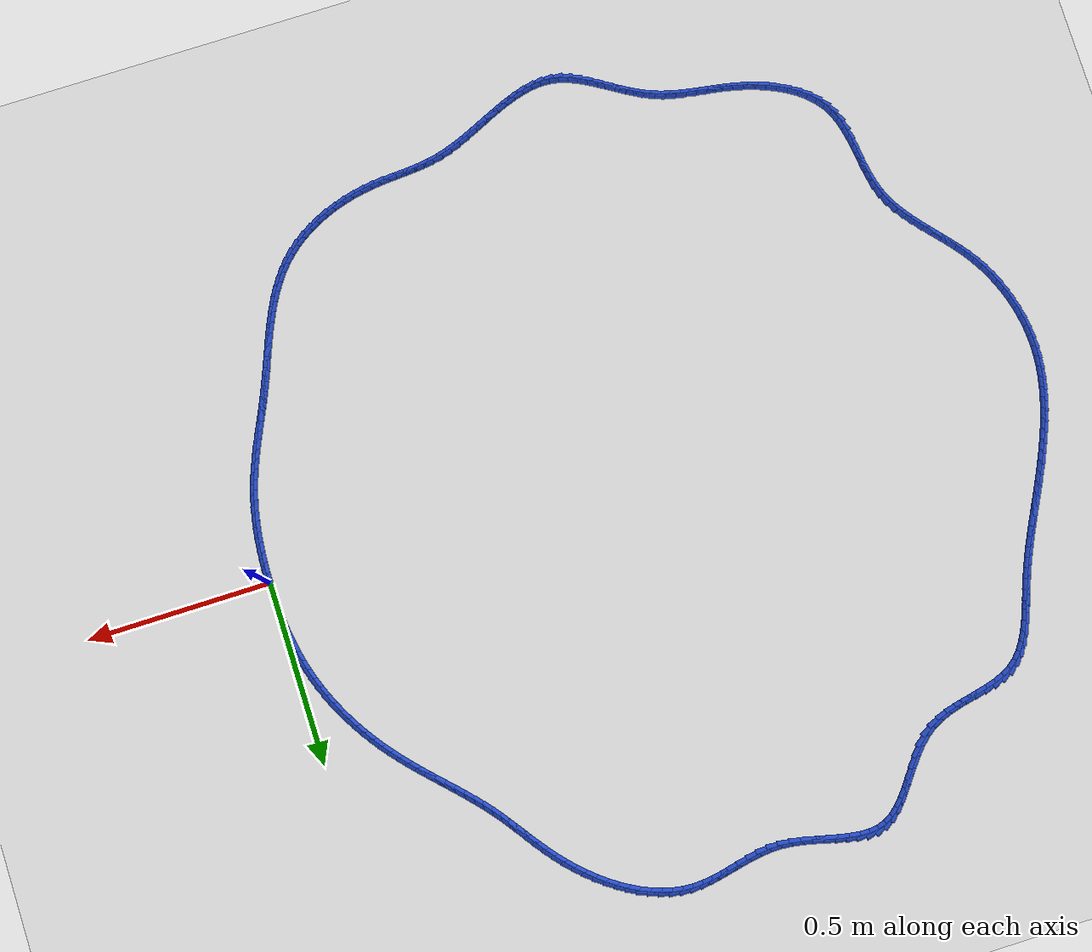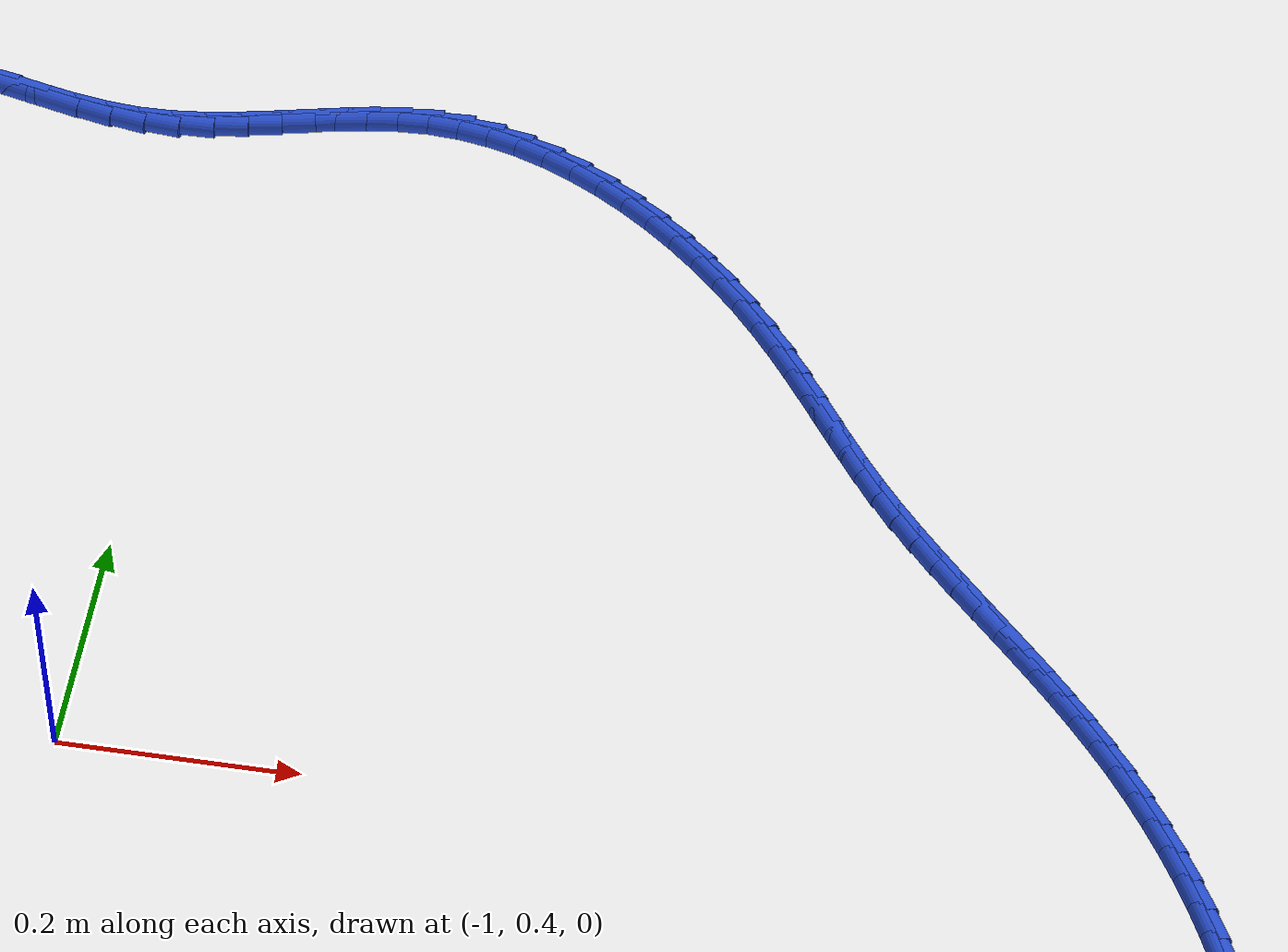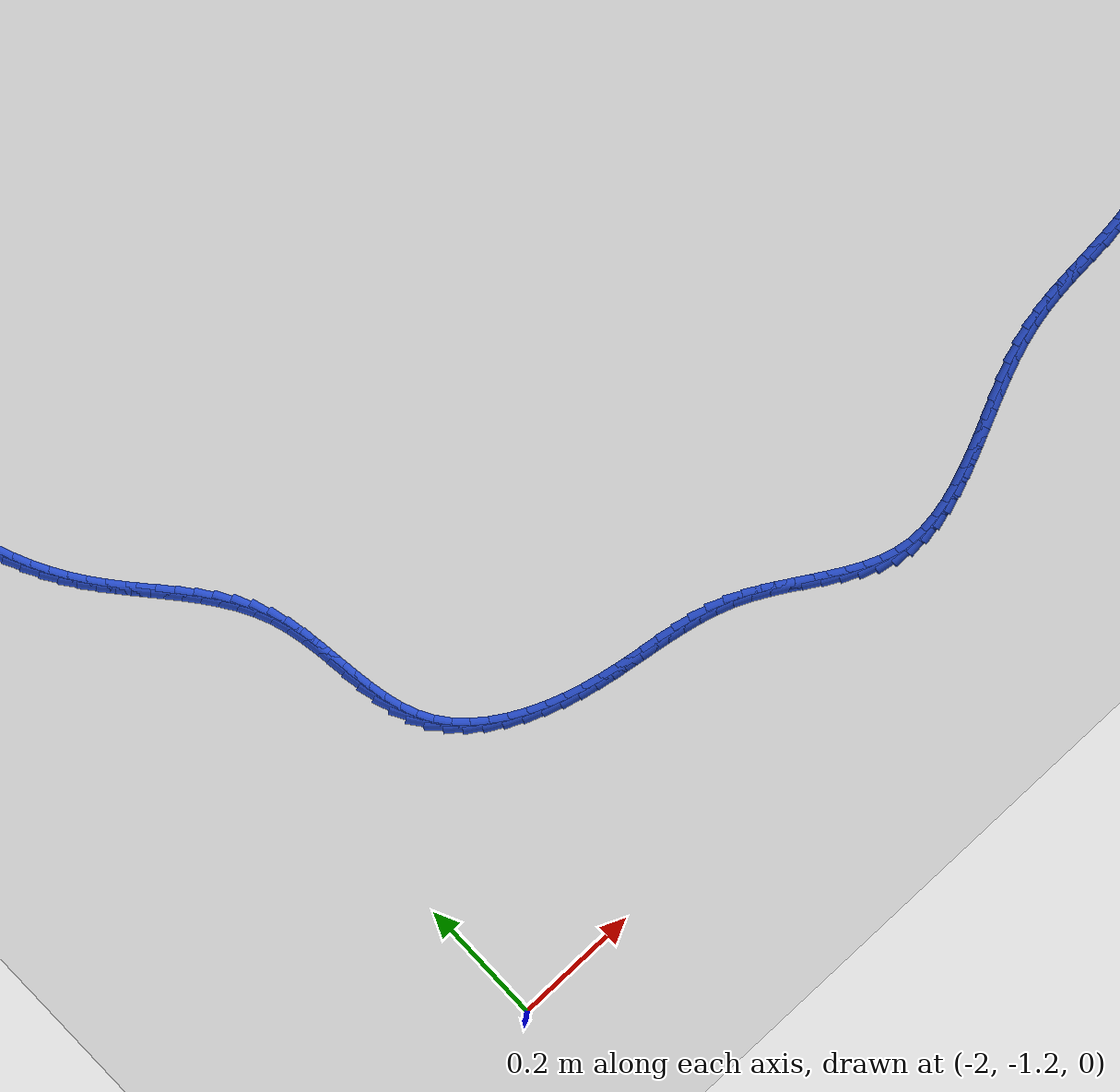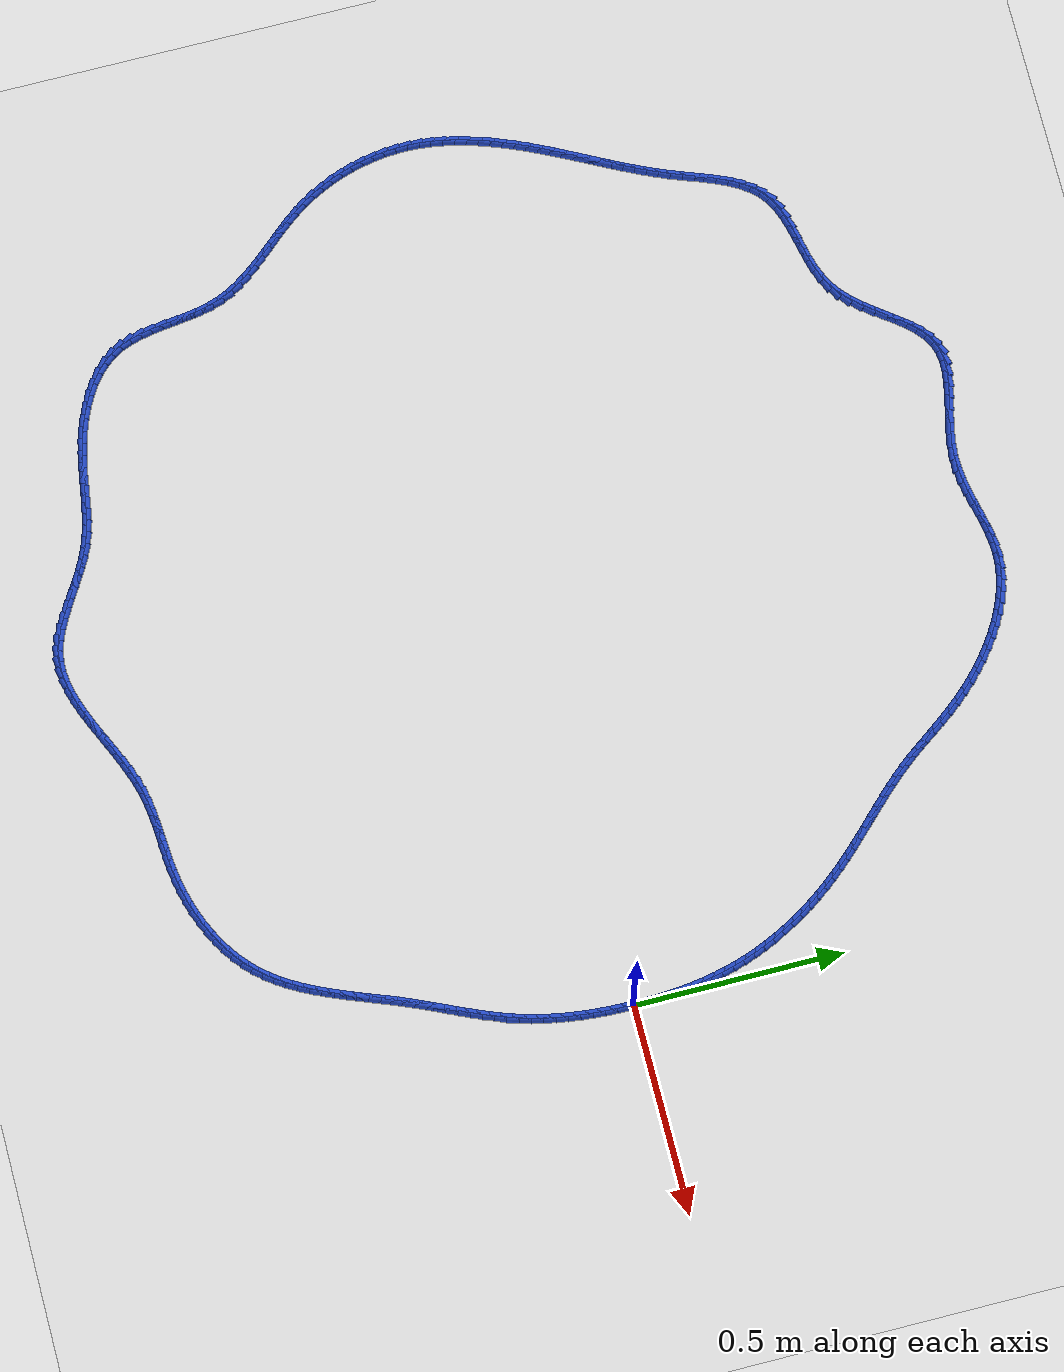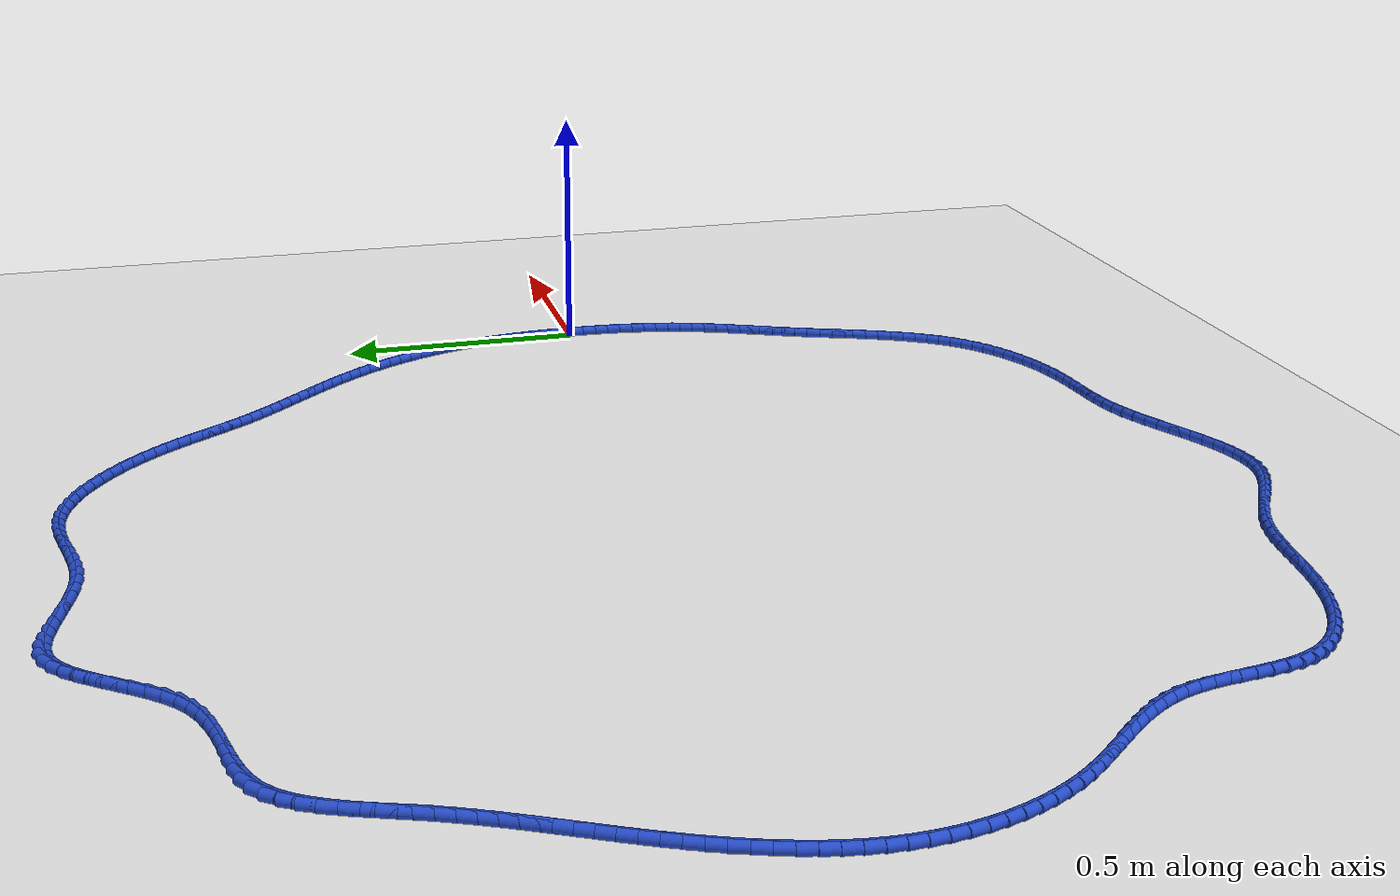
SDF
<sdf version="1.6">
 <world name="default">
  <light name="sun" type="directional">
   <pose>0 0 10 0 -0 0</pose>
   <diffuse>0.8 0.8 0.8 1</diffuse>
   <specular>0.2 0.2 0.2 1</specular>
   <attenuation>
    <range>1000</range>
    <constant>0.9</constant>
    <linear>0.01</linear>
    <quadratic>0.001</quadratic>
   </attenuation>
   <direction>-0.5 0.1 -0.9</direction>
  </light>
  <model name="ground_plane">
   <static>1</static>
   <link name="link">
    <collision name="collision">
     <geometry><plane><normal>0 0 1</normal><size>100 100</size></plane></geometry>
     <surface><friction><ode><mu>100</mu><mu2>50</mu2></ode></friction></surface>
    </collision>
    <visual name="visual">
     <cast_shadows>0</cast_shadows>
     <geometry><plane><normal>0 0 1</normal><size>100 100</size></plane></geometry>
     <material>
      <script><uri>file://media/materials/scripts/gazebo.material</uri><name>Gazebo/WhiteGlow</name></script>
     </material>
    </visual>
   </link>
  </model>
  <gravity>0 0 -9.8</gravity>
  <magnetic_field>6e-06 2.3e-05 -4.2e-05</magnetic_field>
  <atmosphere type="adiabatic"/>
  <physics name="default_physics" default="0" type="ode">
   <max_step_size>0.001</max_step_size>
   <real_time_factor>1</real_time_factor>
   <real_time_update_rate>1000</real_time_update_rate>
  </physics>
  <scene><ambient>0.4 0.4 0.4 1</ambient><background>0.7 0.7 0.7 1</background><shadows>1</shadows></scene>
  <spherical_coordinates>
   <surface_model>EARTH_WGS84</surface_model>
   <latitude_deg>0</latitude_deg>
   <longitude_deg>0</longitude_deg>
   <elevation>0</elevation>
   <heading_deg>0</heading_deg>
  </spherical_coordinates>
  <model name="line">
   <link name="link_0">
    <pose>-6.938893903907228e-18 -1.3877787807814457e-17 0.01 0 1.57 -1.5612643163533644</pose>
    <collision name="collision">
     <geometry><cylinder><radius>0.01</radius><length>0.08</length></cylinder></geometry>
    </collision>
    <visual name="visual">
     <material>
      <script><name>Gazebo/Blue</name><uri>file://media/materials/scripts/gazebo.material</uri></script>
     </material>
     <geometry><cylinder><radius>0.01</radius><length>0.08</length></cylinder></geometry>
    </visual>
   </link>
   <link name="link_1">
    <pose>-0.00027130869325891474 0.028462041445249442 0.01 0 1.57 -1.5373945248930927</pose>
    <collision name="collision">
     <geometry><cylinder><radius>0.01</radius><length>0.08</length></cylinder></geometry>
    </collision>
    <visual name="visual">
     <material>
      <script><name>Gazebo/Blue</name><uri>file://media/materials/scripts/gazebo.material</uri></script>
     </material>
     <geometry><cylinder><radius>0.01</radius><length>0.08</length></cylinder></geometry>
    </visual>
   </link>
   <link name="link_2">
    <pose>-0.0012205438768052683 0.05687015384956497 0.01 0 1.57 -1.5113053776381165</pose>
    <collision name="collision">
     <geometry><cylinder><radius>0.01</radius><length>0.08</length></cylinder></geometry>
    </collision>
    <visual name="visual">
     <material>
      <script><name>Gazebo/Blue</name><uri>file://media/materials/scripts/gazebo.material</uri></script>
     </material>
     <geometry><cylinder><radius>0.01</radius><length>0.08</length></cylinder></geometry>
    </visual>
   </link>
   <link name="link_3">
    <pose>-0.002907398803572792 0.08519151125153555 0.01 0 1.57 -1.4829375800047557</pose>
    <collision name="collision">
     <geometry><cylinder><radius>0.01</radius><length>0.08</length></cylinder></geometry>
    </collision>
    <visual name="visual">
     <material>
      <script><name>Gazebo/Blue</name><uri>file://media/materials/scripts/gazebo.material</uri></script>
     </material>
     <geometry><cylinder><radius>0.01</radius><length>0.08</length></cylinder></geometry>
    </visual>
   </link>
   <link name="link_4">
    <pose>-0.005391566726495208 0.1133932876897502 0.01 0 1.57 -1.4522373443009398</pose>
    <collision name="collision">
     <geometry><cylinder><radius>0.01</radius><length>0.08</length></cylinder></geometry>
    </collision>
    <visual name="visual">
     <material>
      <script><name>Gazebo/Blue</name><uri>file://media/materials/scripts/gazebo.material</uri></script>
     </material>
     <geometry><cylinder><radius>0.01</radius><length>0.08</length></cylinder></geometry>
    </visual>
   </link>
   <link name="link_5">
    <pose>-0.008732740898506248 0.14144265720279794 0.01 0 1.57 -1.41916093189884</pose>
    <collision name="collision">
     <geometry><cylinder><radius>0.01</radius><length>0.08</length></cylinder></geometry>
    </collision>
    <visual name="visual">
     <material>
      <script><name>Gazebo/Blue</name><uri>file://media/materials/scripts/gazebo.material</uri></script>
     </material>
     <geometry><cylinder><radius>0.01</radius><length>0.08</length></cylinder></geometry>
    </visual>
   </link>
   <link name="link_6">
    <pose>-0.012990614572539635 0.16930679382926783 0.01 0 1.57 -1.3836799098387143</pose>
    <collision name="collision">
     <geometry><cylinder><radius>0.01</radius><length>0.08</length></cylinder></geometry>
    </collision>
    <visual name="visual">
     <material>
      <script><name>Gazebo/Blue</name><uri>file://media/materials/scripts/gazebo.material</uri></script>
     </material>
     <geometry><cylinder><radius>0.01</radius><length>0.08</length></cylinder></geometry>
    </visual>
   </link>
   <link name="link_7">
    <pose>-0.01822488100152909 0.19695287160774877 0.01 0 1.57 -1.3457870482247185</pose>
    <collision name="collision">
     <geometry><cylinder><radius>0.01</radius><length>0.08</length></cylinder></geometry>
    </collision>
    <visual name="visual">
     <material>
      <script><name>Gazebo/Blue</name><uri>file://media/materials/scripts/gazebo.material</uri></script>
     </material>
     <geometry><cylinder><radius>0.01</radius><length>0.08</length></cylinder></geometry>
    </visual>
   </link>
   <link name="link_8">
    <pose>-0.024495233438408336 0.22434806457682985 0.01 0 1.57 -1.305502673380487</pose>
    <collision name="collision">
     <geometry><cylinder><radius>0.01</radius><length>0.08</length></cylinder></geometry>
    </collision>
    <visual name="visual">
     <material>
      <script><name>Gazebo/Blue</name><uri>file://media/materials/scripts/gazebo.material</uri></script>
     </material>
     <geometry><cylinder><radius>0.01</radius><length>0.08</length></cylinder></geometry>
    </visual>
   </link>
   <link name="link_9">
    <pose>-0.03186136513611111 0.25145954677509996 0.01 0 1.57 -1.2631181528108952</pose>
    <collision name="collision">
     <geometry><cylinder><radius>0.01</radius><length>0.08</length></cylinder></geometry>
    </collision>
    <visual name="visual">
     <material>
      <script><name>Gazebo/Blue</name><uri>file://media/materials/scripts/gazebo.material</uri></script>
     </material>
     <geometry><cylinder><radius>0.01</radius><length>0.08</length></cylinder></geometry>
    </visual>
   </link>
   <link name="link_10">
    <pose>-0.040376124784414734 0.27825495685794466 0.01 0 1.57 -1.2209208079159697</pose>
    <collision name="collision">
     <geometry><cylinder><radius>0.01</radius><length>0.08</length></cylinder></geometry>
    </collision>
    <visual name="visual">
     <material>
      <script><name>Gazebo/Blue</name><uri>file://media/materials/scripts/gazebo.material</uri></script>
     </material>
     <geometry><cylinder><radius>0.01</radius><length>0.08</length></cylinder></geometry>
    </visual>
   </link>
   <link name="link_11">
    <pose>-0.05002789106515003 0.3047063097788222 0.01 0 1.57 -1.1801161569599878</pose>
    <collision name="collision">
     <geometry><cylinder><radius>0.01</radius><length>0.08</length></cylinder></geometry>
    </collision>
    <visual name="visual">
     <material>
      <script><name>Gazebo/Blue</name><uri>file://media/materials/scripts/gazebo.material</uri></script>
     </material>
     <geometry><cylinder><radius>0.01</radius><length>0.08</length></cylinder></geometry>
    </visual>
   </link>
   <link name="link_12">
    <pose>-0.060769650710284534 0.3307880229373348 0.01 0 1.57 -1.1406677091465236</pose>
    <collision name="collision">
     <geometry><cylinder><radius>0.01</radius><length>0.08</length></cylinder></geometry>
    </collision>
    <visual name="visual">
     <material>
      <script><name>Gazebo/Blue</name><uri>file://media/materials/scripts/gazebo.material</uri></script>
     </material>
     <geometry><cylinder><radius>0.01</radius><length>0.08</length></cylinder></geometry>
    </visual>
   </link>
   <link name="link_13">
    <pose>-0.07255402562769962 0.35647453849776206 0.01 0 1.57 -1.102513482948305</pose>
    <collision name="collision">
     <geometry><cylinder><radius>0.01</radius><length>0.08</length></cylinder></geometry>
    </collision>
    <visual name="visual">
     <material>
      <script><name>Gazebo/Blue</name><uri>file://media/materials/scripts/gazebo.material</uri></script>
     </material>
     <geometry><cylinder><radius>0.01</radius><length>0.08</length></cylinder></geometry>
    </visual>
   </link>
   <link name="link_14">
    <pose>-0.08533363772527677 0.3817402986243835 0.01 0 1.57 -1.065581280114113</pose>
    <collision name="collision">
     <geometry><cylinder><radius>0.01</radius><length>0.08</length></cylinder></geometry>
    </collision>
    <visual name="visual">
     <material>
      <script><name>Gazebo/Blue</name><uri>file://media/materials/scripts/gazebo.material</uri></script>
     </material>
     <geometry><cylinder><radius>0.01</radius><length>0.08</length></cylinder></geometry>
    </visual>
   </link>
   <link name="link_15">
    <pose>-0.09906110891089742 0.4065597454814788 0.01 0 1.57 -1.029790951482598</pose>
    <collision name="collision">
     <geometry><cylinder><radius>0.01</radius><length>0.08</length></cylinder></geometry>
    </collision>
    <visual name="visual">
     <material>
      <script><name>Gazebo/Blue</name><uri>file://media/materials/scripts/gazebo.material</uri></script>
     </material>
     <geometry><cylinder><radius>0.01</radius><length>0.08</length></cylinder></geometry>
    </visual>
   </link>
   <link name="link_16">
    <pose>-0.11368906109244299 0.4309073212333273 0.01 0 1.57 -0.9950562739901385</pose>
    <collision name="collision">
     <geometry><cylinder><radius>0.01</radius><length>0.08</length></cylinder></geometry>
    </collision>
    <visual name="visual">
     <material>
      <script><name>Gazebo/Blue</name><uri>file://media/materials/scripts/gazebo.material</uri></script>
     </material>
     <geometry><cylinder><radius>0.01</radius><length>0.08</length></cylinder></geometry>
    </visual>
   </link>
   <link name="link_17">
    <pose>-0.12917011617779495 0.4547574680442089 0.01 0 1.57 -0.961286447997593</pose>
    <collision name="collision">
     <geometry><cylinder><radius>0.01</radius><length>0.08</length></cylinder></geometry>
    </collision>
    <visual name="visual">
     <material>
      <script><name>Gazebo/Blue</name><uri>file://media/materials/scripts/gazebo.material</uri></script>
     </material>
     <geometry><cylinder><radius>0.01</radius><length>0.08</length></cylinder></geometry>
    </visual>
   </link>
   <link name="link_18">
    <pose>-0.14545689607483472 0.478084628078403 0.01 0 1.57 -0.9283872384600935</pose>
    <collision name="collision">
     <geometry><cylinder><radius>0.01</radius><length>0.08</length></cylinder></geometry>
    </collision>
    <visual name="visual">
     <material>
      <script><name>Gazebo/Blue</name><uri>file://media/materials/scripts/gazebo.material</uri></script>
     </material>
     <geometry><cylinder><radius>0.01</radius><length>0.08</length></cylinder></geometry>
    </visual>
   </link>
   <link name="link_19">
    <pose>-0.16250202269144373 0.5008632435001891 0.01 0 1.57 -0.8962617910761358</pose>
    <collision name="collision">
     <geometry><cylinder><radius>0.01</radius><length>0.08</length></cylinder></geometry>
    </collision>
    <visual name="visual">
     <material>
      <script><name>Gazebo/Blue</name><uri>file://media/materials/scripts/gazebo.material</uri></script>
     </material>
     <geometry><cylinder><radius>0.01</radius><length>0.08</length></cylinder></geometry>
    </visual>
   </link>
   <link name="link_20">
    <pose>-0.18025811793550345 0.5230677564738471 0.01 0 1.57 -0.8653883867662681</pose>
    <collision name="collision">
     <geometry><cylinder><radius>0.01</radius><length>0.08</length></cylinder></geometry>
    </collision>
    <visual name="visual">
     <material>
      <script><name>Gazebo/Blue</name><uri>file://media/materials/scripts/gazebo.material</uri></script>
     </material>
     <geometry><cylinder><radius>0.01</radius><length>0.08</length></cylinder></geometry>
    </visual>
   </link>
   <link name="link_21">
    <pose>-0.19866852991135206 0.5446869959581031 0.01 0 1.57 -0.8391510652437308</pose>
    <collision name="collision">
     <geometry><cylinder><radius>0.01</radius><length>0.08</length></cylinder></geometry>
    </collision>
    <visual name="visual">
     <material>
      <script><name>Gazebo/Blue</name><uri>file://media/materials/scripts/gazebo.material</uri></script>
     </material>
     <geometry><cylinder><radius>0.01</radius><length>0.08</length></cylinder></geometry>
    </visual>
   </link>
   <link name="link_22">
    <pose>-0.21762143214830776 0.5657953852706543 0.01 0 1.57 -0.8188360638029999</pose>
    <collision name="collision">
     <geometry><cylinder><radius>0.01</radius><length>0.08</length></cylinder></geometry>
    </collision>
    <visual name="visual">
     <material>
      <script><name>Gazebo/Blue</name><uri>file://media/materials/scripts/gazebo.material</uri></script>
     </material>
     <geometry><cylinder><radius>0.01</radius><length>0.08</length></cylinder></geometry>
    </visual>
   </link>
   <link name="link_23">
    <pose>-0.2369846752825213 0.586498875385052 0.01 0 1.57 -0.8044536521222202</pose>
    <collision name="collision">
     <geometry><cylinder><radius>0.01</radius><length>0.08</length></cylinder></geometry>
    </collision>
    <visual name="visual">
     <material>
      <script><name>Gazebo/Blue</name><uri>file://media/materials/scripts/gazebo.material</uri></script>
     </material>
     <geometry><cylinder><radius>0.01</radius><length>0.08</length></cylinder></geometry>
    </visual>
   </link>
   <link name="link_24">
    <pose>-0.25662607814597316 0.6069034666138325 0.01 0 1.57 -0.7960057918467021</pose>
    <collision name="collision">
     <geometry><cylinder><radius>0.01</radius><length>0.08</length></cylinder></geometry>
    </collision>
    <visual name="visual">
     <material>
      <script><name>Gazebo/Blue</name><uri>file://media/materials/scripts/gazebo.material</uri></script>
     </material>
     <geometry><cylinder><radius>0.01</radius><length>0.08</length></cylinder></geometry>
    </visual>
   </link>
   <link name="link_25">
    <pose>-0.2764134595706434 0.6271151592695328 0.01 0 1.57 -0.793503375734931</pose>
    <collision name="collision">
     <geometry><cylinder><radius>0.01</radius><length>0.08</length></cylinder></geometry>
    </collision>
    <visual name="visual">
     <material>
      <script><name>Gazebo/Blue</name><uri>file://media/materials/scripts/gazebo.material</uri></script>
     </material>
     <geometry><cylinder><radius>0.01</radius><length>0.08</length></cylinder></geometry>
    </visual>
   </link>
   <link name="link_26">
    <pose>-0.29621463838851253 0.6472399536646894 0.01 0 1.57 -0.7969753440775542</pose>
    <collision name="collision">
     <geometry><cylinder><radius>0.01</radius><length>0.08</length></cylinder></geometry>
    </collision>
    <visual name="visual">
     <material>
      <script><name>Gazebo/Blue</name><uri>file://media/materials/scripts/gazebo.material</uri></script>
     </material>
     <geometry><cylinder><radius>0.01</radius><length>0.08</length></cylinder></geometry>
    </visual>
   </link>
   <link name="link_27">
    <pose>-0.31589743343156085 0.6673838501118394 0.01 0 1.57 -0.8064716883965122</pose>
    <collision name="collision">
     <geometry><cylinder><radius>0.01</radius><length>0.08</length></cylinder></geometry>
    </collision>
    <visual name="visual">
     <material>
      <script><name>Gazebo/Blue</name><uri>file://media/materials/scripts/gazebo.material</uri></script>
     </material>
     <geometry><cylinder><radius>0.01</radius><length>0.08</length></cylinder></geometry>
    </visual>
   </link>
   <link name="link_28">
    <pose>-0.3353296635317688 0.6876528489235193 0.01 0 1.57 -0.8220601788648326</pose>
    <collision name="collision">
     <geometry><cylinder><radius>0.01</radius><length>0.08</length></cylinder></geometry>
    </collision>
    <visual name="visual">
     <material>
      <script><name>Gazebo/Blue</name><uri>file://media/materials/scripts/gazebo.material</uri></script>
     </material>
     <geometry><cylinder><radius>0.01</radius><length>0.08</length></cylinder></geometry>
    </visual>
   </link>
   <link name="link_29">
    <pose>-0.3543791475211166 0.7081529504122661 0.01 0 1.57 -0.8438163722057962</pose>
    <collision name="collision">
     <geometry><cylinder><radius>0.01</radius><length>0.08</length></cylinder></geometry>
    </collision>
    <visual name="visual">
     <material>
      <script><name>Gazebo/Blue</name><uri>file://media/materials/scripts/gazebo.material</uri></script>
     </material>
     <geometry><cylinder><radius>0.01</radius><length>0.08</length></cylinder></geometry>
    </visual>
   </link>
   <link name="link_30">
    <pose>-0.3729137042315846 0.7289901548906161 0.01 0 1.57 -0.8718062589909729</pose>
    <collision name="collision">
     <geometry><cylinder><radius>0.01</radius><length>0.08</length></cylinder></geometry>
    </collision>
    <visual name="visual">
     <material>
      <script><name>Gazebo/Blue</name><uri>file://media/materials/scripts/gazebo.material</uri></script>
     </material>
     <geometry><cylinder><radius>0.01</radius><length>0.08</length></cylinder></geometry>
    </visual>
   </link>
   <link name="link_31">
    <pose>-0.39080115249515324 0.7502704626711066 0.01 0 1.57 -0.9043122076625909</pose>
    <collision name="collision">
     <geometry><cylinder><radius>0.01</radius><length>0.08</length></cylinder></geometry>
    </collision>
    <visual name="visual">
     <material>
      <script><name>Gazebo/Blue</name><uri>file://media/materials/scripts/gazebo.material</uri></script>
     </material>
     <geometry><cylinder><radius>0.01</radius><length>0.08</length></cylinder></geometry>
    </visual>
   </link>
   <link name="link_32">
    <pose>-0.40795145854143117 0.7720750059246441 0.01 0 1.57 -0.9299000270597352</pose>
    <collision name="collision">
     <geometry><cylinder><radius>0.01</radius><length>0.08</length></cylinder></geometry>
    </collision>
    <visual name="visual">
     <material>
      <script><name>Gazebo/Blue</name><uri>file://media/materials/scripts/gazebo.material</uri></script>
     </material>
     <geometry><cylinder><radius>0.01</radius><length>0.08</length></cylinder></geometry>
    </visual>
   </link>
   <link name="link_33">
    <pose>-0.4245476706668413 0.7943237907764882 0.01 0 1.57 -0.9438922300333664</pose>
    <collision name="collision">
     <geometry><cylinder><radius>0.01</radius><length>0.08</length></cylinder></geometry>
    </collision>
    <visual name="visual">
     <material>
      <script><name>Gazebo/Blue</name><uri>file://media/materials/scripts/gazebo.material</uri></script>
     </material>
     <geometry><cylinder><radius>0.01</radius><length>0.08</length></cylinder></geometry>
    </visual>
   </link>
   <link name="link_34">
    <pose>-0.4408816676187621 0.8168726103465814 0.01 0 1.57 -0.9462885794864765</pose>
    <collision name="collision">
     <geometry><cylinder><radius>0.01</radius><length>0.08</length></cylinder></geometry>
    </collision>
    <visual name="visual">
     <material>
      <script><name>Gazebo/Blue</name><uri>file://media/materials/scripts/gazebo.material</uri></script>
     </material>
     <geometry><cylinder><radius>0.01</radius><length>0.08</length></cylinder></geometry>
    </visual>
   </link>
   <link name="link_35">
    <pose>-0.45724560960467747 0.8395770916855434 0.01 0 1.57 -0.9372516686920985</pose>
    <collision name="collision">
     <geometry><cylinder><radius>0.01</radius><length>0.08</length></cylinder></geometry>
    </collision>
    <visual name="visual">
     <material>
      <script><name>Gazebo/Blue</name><uri>file://media/materials/scripts/gazebo.material</uri></script>
     </material>
     <geometry><cylinder><radius>0.01</radius><length>0.08</length></cylinder></geometry>
    </visual>
   </link>
   <link name="link_36">
    <pose>-0.47393165683207095 0.862292861843994 0.01 0 1.57 -0.9170784924777136</pose>
    <collision name="collision">
     <geometry><cylinder><radius>0.01</radius><length>0.08</length></cylinder></geometry>
    </collision>
    <visual name="visual">
     <material>
      <script><name>Gazebo/Blue</name><uri>file://media/materials/scripts/gazebo.material</uri></script>
     </material>
     <geometry><cylinder><radius>0.01</radius><length>0.08</length></cylinder></geometry>
    </visual>
   </link>
   <link name="link_37">
    <pose>-0.49123196950842685 0.8848755478725536 0.01 0 1.57 -0.8862225286952782</pose>
    <collision name="collision">
     <geometry><cylinder><radius>0.01</radius><length>0.08</length></cylinder></geometry>
    </collision>
    <visual name="visual">
     <material>
      <script><name>Gazebo/Blue</name><uri>file://media/materials/scripts/gazebo.material</uri></script>
     </material>
     <geometry><cylinder><radius>0.01</radius><length>0.08</length></cylinder></geometry>
    </visual>
   </link>
   <link name="link_38">
    <pose>-0.5094387078412288 0.9071807768218415 0.01 0 1.57 -0.8458173345315733</pose>
    <collision name="collision">
     <geometry><cylinder><radius>0.01</radius><length>0.08</length></cylinder></geometry>
    </collision>
    <visual name="visual">
     <material>
      <script><name>Gazebo/Blue</name><uri>file://media/materials/scripts/gazebo.material</uri></script>
     </material>
     <geometry><cylinder><radius>0.01</radius><length>0.08</length></cylinder></geometry>
    </visual>
   </link>
   <link name="link_39">
    <pose>-0.5288231600094285 0.9290614733010362 0.01 0 1.57 -0.8015394465039641</pose>
    <collision name="collision">
     <geometry><cylinder><radius>0.01</radius><length>0.08</length></cylinder></geometry>
    </collision>
    <visual name="visual">
     <material>
      <script><name>Gazebo/Blue</name><uri>file://media/materials/scripts/gazebo.material</uri></script>
     </material>
     <geometry><cylinder><radius>0.01</radius><length>0.08</length></cylinder></geometry>
    </visual>
   </link>
   <link name="link_40">
    <pose>-0.5494263380062694 0.9503407465179796 0.01 0 1.57 -0.7560822204926323</pose>
    <collision name="collision">
     <geometry><cylinder><radius>0.01</radius><length>0.08</length></cylinder></geometry>
    </collision>
    <visual name="visual">
     <material>
      <script><name>Gazebo/Blue</name><uri>file://media/materials/scripts/gazebo.material</uri></script>
     </material>
     <geometry><cylinder><radius>0.01</radius><length>0.08</length></cylinder></geometry>
    </visual>
   </link>
   <link name="link_41">
    <pose>-0.5711463549652865 0.970823203607279 0.01 0 1.57 -0.7087451567530947</pose>
    <collision name="collision">
     <geometry><cylinder><radius>0.01</radius><length>0.08</length></cylinder></geometry>
    </collision>
    <visual name="visual">
     <material>
      <script><name>Gazebo/Blue</name><uri>file://media/materials/scripts/gazebo.material</uri></script>
     </material>
     <geometry><cylinder><radius>0.01</radius><length>0.08</length></cylinder></geometry>
    </visual>
   </link>
   <link name="link_42">
    <pose>-0.5938791844812488 0.9903131746831142 0.01 0 1.57 -0.6587697727177344</pose>
    <collision name="collision">
     <geometry><cylinder><radius>0.01</radius><length>0.08</length></cylinder></geometry>
    </collision>
    <visual name="visual">
     <material>
      <script><name>Gazebo/Blue</name><uri>file://media/materials/scripts/gazebo.material</uri></script>
     </material>
     <geometry><cylinder><radius>0.01</radius><length>0.08</length></cylinder></geometry>
    </visual>
   </link>
   <link name="link_43">
    <pose>-0.6175208001489252 1.0086149898596664 0.01 0 1.57 -0.6053669931212564</pose>
    <collision name="collision">
     <geometry><cylinder><radius>0.01</radius><length>0.08</length></cylinder></geometry>
    </collision>
    <visual name="visual">
     <material>
      <script><name>Gazebo/Blue</name><uri>file://media/materials/scripts/gazebo.material</uri></script>
     </material>
     <geometry><cylinder><radius>0.01</radius><length>0.08</length></cylinder></geometry>
    </visual>
   </link>
   <link name="link_44">
    <pose>-0.6419671755630845 1.0255329792511159 0.01 0 1.57 -0.5477039994844735</pose>
    <collision name="collision">
     <geometry><cylinder><radius>0.01</radius><length>0.08</length></cylinder></geometry>
    </collision>
    <visual name="visual">
     <material>
      <script><name>Gazebo/Blue</name><uri>file://media/materials/scripts/gazebo.material</uri></script>
     </material>
     <geometry><cylinder><radius>0.01</radius><length>0.08</length></cylinder></geometry>
    </visual>
   </link>
   <link name="link_45">
    <pose>-0.6671142843184957 1.0408714729716435 0.01 0 1.57 -0.48490221312924486</pose>
    <collision name="collision">
     <geometry><cylinder><radius>0.01</radius><length>0.08</length></cylinder></geometry>
    </collision>
    <visual name="visual">
     <material>
      <script><name>Gazebo/Blue</name><uri>file://media/materials/scripts/gazebo.material</uri></script>
     </material>
     <geometry><cylinder><radius>0.01</radius><length>0.08</length></cylinder></geometry>
    </visual>
   </link>
   <link name="link_46">
    <pose>-0.6928581000099273 1.05443480113543 0.01 0 1.57 -0.4160524611614517</pose>
    <collision name="collision">
     <geometry><cylinder><radius>0.01</radius><length>0.08</length></cylinder></geometry>
    </collision>
    <visual name="visual">
     <material>
      <script><name>Gazebo/Blue</name><uri>file://media/materials/scripts/gazebo.material</uri></script>
     </material>
     <geometry><cylinder><radius>0.01</radius><length>0.08</length></cylinder></geometry>
    </visual>
   </link>
   <link name="link_47">
    <pose>-0.7190945962321491 1.0660272938566564 0.01 0 1.57 -0.3402566744808497</pose>
    <collision name="collision">
     <geometry><cylinder><radius>0.01</radius><length>0.08</length></cylinder></geometry>
    </collision>
    <visual name="visual">
     <material>
      <script><name>Gazebo/Blue</name><uri>file://media/materials/scripts/gazebo.material</uri></script>
     </material>
     <geometry><cylinder><radius>0.01</radius><length>0.08</length></cylinder></geometry>
    </visual>
   </link>
   <link name="link_48">
    <pose>-0.7457197465799293 1.0754532812495032 0.01 0 1.57 -0.25670817175495614</pose>
    <collision name="collision">
     <geometry><cylinder><radius>0.01</radius><length>0.08</length></cylinder></geometry>
    </collision>
    <visual name="visual">
     <material>
      <script><name>Gazebo/Blue</name><uri>file://media/materials/scripts/gazebo.material</uri></script>
     </material>
     <geometry><cylinder><radius>0.01</radius><length>0.08</length></cylinder></geometry>
    </visual>
   </link>
   <link name="link_49">
    <pose>-0.7726295246480367 1.0825170934281505 0.01 0 1.57 -0.16482196395519444</pose>
    <collision name="collision">
     <geometry><cylinder><radius>0.01</radius><length>0.08</length></cylinder></geometry>
    </collision>
    <visual name="visual">
     <material>
      <script><name>Gazebo/Blue</name><uri>file://media/materials/scripts/gazebo.material</uri></script>
     </material>
     <geometry><cylinder><radius>0.01</radius><length>0.08</length></cylinder></geometry>
    </visual>
   </link>
   <link name="link_50">
    <pose>-0.7997199040312409 1.0870230605067799 0.01 0 1.57 -0.06441750527427997</pose>
    <collision name="collision">
     <geometry><cylinder><radius>0.01</radius><length>0.08</length></cylinder></geometry>
    </collision>
    <visual name="visual">
     <material>
      <script><name>Gazebo/Blue</name><uri>file://media/materials/scripts/gazebo.material</uri></script>
     </material>
     <geometry><cylinder><radius>0.01</radius><length>0.08</length></cylinder></geometry>
    </visual>
   </link>
   <link name="link_51">
    <pose>-0.8268868583243099 1.0887755125995715 0.01 0 1.57 0.03873584492412755</pose>
    <collision name="collision">
     <geometry><cylinder><radius>0.01</radius><length>0.08</length></cylinder></geometry>
    </collision>
    <visual name="visual">
     <material>
      <script><name>Gazebo/Blue</name><uri>file://media/materials/scripts/gazebo.material</uri></script>
     </material>
     <geometry><cylinder><radius>0.01</radius><length>0.08</length></cylinder></geometry>
    </visual>
   </link>
   <link name="link_52">
    <pose>-0.8540537548840204 1.08772265326158 0.01 0 1.57 0.12177452792422636</pose>
    <collision name="collision">
     <geometry><cylinder><radius>0.01</radius><length>0.08</length></cylinder></geometry>
    </collision>
    <visual name="visual">
     <material>
      <script><name>Gazebo/Blue</name><uri>file://media/materials/scripts/gazebo.material</uri></script>
     </material>
     <geometry><cylinder><radius>0.01</radius><length>0.08</length></cylinder></geometry>
    </visual>
   </link>
   <link name="link_53">
    <pose>-0.8812546083747644 1.084393811373627 0.01 0 1.57 0.17863850483599505</pose>
    <collision name="collision">
     <geometry><cylinder><radius>0.01</radius><length>0.08</length></cylinder></geometry>
    </collision>
    <visual name="visual">
     <material>
      <script><name>Gazebo/Blue</name><uri>file://media/materials/scripts/gazebo.material</uri></script>
     </material>
     <geometry><cylinder><radius>0.01</radius><length>0.08</length></cylinder></geometry>
    </visual>
   </link>
   <link name="link_54">
    <pose>-0.9085513659707032 1.0794650187882342 0.01 0 1.57 0.21003375993049386</pose>
    <collision name="collision">
     <geometry><cylinder><radius>0.01</radius><length>0.08</length></cylinder></geometry>
    </collision>
    <visual name="visual">
     <material>
      <script><name>Gazebo/Blue</name><uri>file://media/materials/scripts/gazebo.material</uri></script>
     </material>
     <geometry><cylinder><radius>0.01</radius><length>0.08</length></cylinder></geometry>
    </visual>
   </link>
   <link name="link_55">
    <pose>-0.9360059748469419 1.0736123073628914 0.01 0 1.57 0.21697174717925855</pose>
    <collision name="collision">
     <geometry><cylinder><radius>0.01</radius><length>0.08</length></cylinder></geometry>
    </collision>
    <visual name="visual">
     <material>
      <script><name>Gazebo/Blue</name><uri>file://media/materials/scripts/gazebo.material</uri></script>
     </material>
     <geometry><cylinder><radius>0.01</radius><length>0.08</length></cylinder></geometry>
    </visual>
   </link>
   <link name="link_56">
    <pose>-0.9636803821785873 1.0675117089550887 0.01 0 1.57 0.2001876166432829</pose>
    <collision name="collision">
     <geometry><cylinder><radius>0.01</radius><length>0.08</length></cylinder></geometry>
    </collision>
    <visual name="visual">
     <material>
      <script><name>Gazebo/Blue</name><uri>file://media/materials/scripts/gazebo.material</uri></script>
     </material>
     <geometry><cylinder><radius>0.01</radius><length>0.08</length></cylinder></geometry>
    </visual>
   </link>
   <link name="link_57">
    <pose>-0.9916365351407457 1.0618392554223173 0.01 0 1.57 0.16004349444617016</pose>
    <collision name="collision">
     <geometry><cylinder><radius>0.01</radius><length>0.08</length></cylinder></geometry>
    </collision>
    <visual name="visual">
     <material>
      <script><name>Gazebo/Blue</name><uri>file://media/materials/scripts/gazebo.material</uri></script>
     </material>
     <geometry><cylinder><radius>0.01</radius><length>0.08</length></cylinder></geometry>
    </visual>
   </link>
   <link name="link_58">
    <pose>-1.019936380908523 1.057270978622066 0.01 0 1.57 0.09682296834092433</pose>
    <collision name="collision">
     <geometry><cylinder><radius>0.01</radius><length>0.08</length></cylinder></geometry>
    </collision>
    <visual name="visual">
     <material>
      <script><name>Gazebo/Blue</name><uri>file://media/materials/scripts/gazebo.material</uri></script>
     </material>
     <geometry><cylinder><radius>0.01</radius><length>0.08</length></cylinder></geometry>
    </visual>
   </link>
   <link name="link_59">
    <pose>-1.0486418666570259 1.0544829104118265 0.01 0 1.57 0.011373963055307643</pose>
    <collision name="collision">
     <geometry><cylinder><radius>0.01</radius><length>0.08</length></cylinder></geometry>
    </collision>
    <visual name="visual">
     <material>
      <script><name>Gazebo/Blue</name><uri>file://media/materials/scripts/gazebo.material</uri></script>
     </material>
     <geometry><cylinder><radius>0.01</radius><length>0.08</length></cylinder></geometry>
    </visual>
   </link>
   <link name="link_60">
    <pose>-1.07781493956136 1.054151082649088 0.01 0 1.57 -0.08685383289227389</pose>
    <collision name="collision">
     <geometry><cylinder><radius>0.01</radius><length>0.08</length></cylinder></geometry>
    </collision>
    <visual name="visual">
     <material>
      <script><name>Gazebo/Blue</name><uri>file://media/materials/scripts/gazebo.material</uri></script>
     </material>
     <geometry><cylinder><radius>0.01</radius><length>0.08</length></cylinder></geometry>
    </visual>
   </link>
   <link name="link_61">
    <pose>-1.1074726452328654 1.0567334648053341 0.01 0 1.57 -0.16320058160579007</pose>
    <collision name="collision">
     <geometry><cylinder><radius>0.01</radius><length>0.08</length></cylinder></geometry>
    </collision>
    <visual name="visual">
     <material>
      <script><name>Gazebo/Blue</name><uri>file://media/materials/scripts/gazebo.material</uri></script>
     </material>
     <geometry><cylinder><radius>0.01</radius><length>0.08</length></cylinder></geometry>
    </visual>
   </link>
   <link name="link_62">
    <pose>-1.1374213711710932 1.0616649748893732 0.01 0 1.57 -0.21079241466443946</pose>
    <collision name="collision">
     <geometry><cylinder><radius>0.01</radius><length>0.08</length></cylinder></geometry>
    </collision>
    <visual name="visual">
     <material>
      <script><name>Gazebo/Blue</name><uri>file://media/materials/scripts/gazebo.material</uri></script>
     </material>
     <geometry><cylinder><radius>0.01</radius><length>0.08</length></cylinder></geometry>
    </visual>
   </link>
   <link name="link_63">
    <pose>-1.1674057804091076 1.0680807688681473 0.01 0 1.57 -0.23210038443102482</pose>
    <collision name="collision">
     <geometry><cylinder><radius>0.01</radius><length>0.08</length></cylinder></geometry>
    </collision>
    <visual name="visual">
     <material>
      <script><name>Gazebo/Blue</name><uri>file://media/materials/scripts/gazebo.material</uri></script>
     </material>
     <geometry><cylinder><radius>0.01</radius><length>0.08</length></cylinder></geometry>
    </visual>
   </link>
   <link name="link_64">
    <pose>-1.197170528075788 1.075115964322302 0.01 0 1.57 -0.22778869949655273</pose>
    <collision name="collision">
     <geometry><cylinder><radius>0.01</radius><length>0.08</length></cylinder></geometry>
    </collision>
    <visual name="visual">
     <material>
      <script><name>Gazebo/Blue</name><uri>file://media/materials/scripts/gazebo.material</uri></script>
     </material>
     <geometry><cylinder><radius>0.01</radius><length>0.08</length></cylinder></geometry>
    </visual>
   </link>
   <link name="link_65">
    <pose>-1.226460269300016 1.0819056788324832 0.01 0 1.57 -0.19630020583996</pose>
    <collision name="collision">
     <geometry><cylinder><radius>0.01</radius><length>0.08</length></cylinder></geometry>
    </collision>
    <visual name="visual">
     <material>
      <script><name>Gazebo/Blue</name><uri>file://media/materials/scripts/gazebo.material</uri></script>
     </material>
     <geometry><cylinder><radius>0.01</radius><length>0.08</length></cylinder></geometry>
    </visual>
   </link>
   <link name="link_66">
    <pose>-1.2550196592106724 1.087585029979336 0.01 0 1.57 -0.13353533153890842</pose>
    <collision name="collision">
     <geometry><cylinder><radius>0.01</radius><length>0.08</length></cylinder></geometry>
    </collision>
    <visual name="visual">
     <material>
      <script><name>Gazebo/Blue</name><uri>file://media/materials/scripts/gazebo.material</uri></script>
     </material>
     <geometry><cylinder><radius>0.01</radius><length>0.08</length></cylinder></geometry>
    </visual>
   </link>
   <link name="link_67">
    <pose>-1.2825933529366376 1.0912891353435064 0.01 0 1.57 -0.03279834160013817</pose>
    <collision name="collision">
     <geometry><cylinder><radius>0.01</radius><length>0.08</length></cylinder></geometry>
    </collision>
    <visual name="visual">
     <material>
      <script><name>Gazebo/Blue</name><uri>file://media/materials/scripts/gazebo.material</uri></script>
     </material>
     <geometry><cylinder><radius>0.01</radius><length>0.08</length></cylinder></geometry>
    </visual>
   </link>
   <link name="link_68">
    <pose>-1.3089260056067928 1.0921531125056396 0.01 0 1.57 0.11389546006018933</pose>
    <collision name="collision">
     <geometry><cylinder><radius>0.01</radius><length>0.08</length></cylinder></geometry>
    </collision>
    <visual name="visual">
     <material>
      <script><name>Gazebo/Blue</name><uri>file://media/materials/scripts/gazebo.material</uri></script>
     </material>
     <geometry><cylinder><radius>0.01</radius><length>0.08</length></cylinder></geometry>
    </visual>
   </link>
   <link name="link_69">
    <pose>-1.3337622723500184 1.0893120790463815 0.01 0 1.57 0.31057913154186934</pose>
    <collision name="collision">
     <geometry><cylinder><radius>0.01</radius><length>0.08</length></cylinder></geometry>
    </collision>
    <visual name="visual">
     <material>
      <script><name>Gazebo/Blue</name><uri>file://media/materials/scripts/gazebo.material</uri></script>
     </material>
     <geometry><cylinder><radius>0.01</radius><length>0.08</length></cylinder></geometry>
    </visual>
   </link>
   <link name="link_70">
    <pose>-1.3568473407781851 1.081902552825048 0.01 0 1.57 0.5270692662035266</pose>
    <collision name="collision">
     <geometry><cylinder><radius>0.01</radius><length>0.08</length></cylinder></geometry>
    </collision>
    <visual name="visual">
     <material>
      <script><name>Gazebo/Blue</name><uri>file://media/materials/scripts/gazebo.material</uri></script>
     </material>
     <geometry><cylinder><radius>0.01</radius><length>0.08</length></cylinder></geometry>
    </visual>
   </link>
   <link name="link_71">
    <pose>-1.378105046972801 1.0695308463175381 0.01 0 1.57 0.6972795286389025</pose>
    <collision name="collision">
     <geometry><cylinder><radius>0.01</radius><length>0.08</length></cylinder></geometry>
    </collision>
    <visual name="visual">
     <material>
      <script><name>Gazebo/Blue</name><uri>file://media/materials/scripts/gazebo.material</uri></script>
     </material>
     <geometry><cylinder><radius>0.01</radius><length>0.08</length></cylinder></geometry>
    </visual>
   </link>
   <link name="link_72">
    <pose>-1.3978963240944338 1.0529527128826168 0.01 0 1.57 0.8140084168196782</pose>
    <collision name="collision">
     <geometry><cylinder><radius>0.01</radius><length>0.08</length></cylinder></geometry>
    </collision>
    <visual name="visual">
     <material>
      <script><name>Gazebo/Blue</name><uri>file://media/materials/scripts/gazebo.material</uri></script>
     </material>
     <geometry><cylinder><radius>0.01</radius><length>0.08</length></cylinder></geometry>
    </visual>
   </link>
   <link name="link_73">
    <pose>-1.416647716330988 1.033096444202458 0.01 0 1.57 0.8858924236731311</pose>
    <collision name="collision">
     <geometry><cylinder><radius>0.01</radius><length>0.08</length></cylinder></geometry>
    </collision>
    <visual name="visual">
     <material>
      <script><name>Gazebo/Blue</name><uri>file://media/materials/scripts/gazebo.material</uri></script>
     </material>
     <geometry><cylinder><radius>0.01</radius><length>0.08</length></cylinder></geometry>
    </visual>
   </link>
   <link name="link_74">
    <pose>-1.4347857678703682 1.010890331959236 0.01 0 1.57 0.9210806830847778</pose>
    <collision name="collision">
     <geometry><cylinder><radius>0.01</radius><length>0.08</length></cylinder></geometry>
    </collision>
    <visual name="visual">
     <material>
      <script><name>Gazebo/Blue</name><uri>file://media/materials/scripts/gazebo.material</uri></script>
     </material>
     <geometry><cylinder><radius>0.01</radius><length>0.08</length></cylinder></geometry>
    </visual>
   </link>
   <link name="link_75">
    <pose>-1.4527370229004775 0.9872626678351251 0.01 0 1.57 0.924639017326788</pose>
    <collision name="collision">
     <geometry><cylinder><radius>0.01</radius><length>0.08</length></cylinder></geometry>
    </collision>
    <visual name="visual">
     <material>
      <script><name>Gazebo/Blue</name><uri>file://media/materials/scripts/gazebo.material</uri></script>
     </material>
     <geometry><cylinder><radius>0.01</radius><length>0.08</length></cylinder></geometry>
    </visual>
   </link>
   <link name="link_76">
    <pose>-1.4709280256092212 0.9631417435122996 0.01 0 1.57 0.8984132760125781</pose>
    <collision name="collision">
     <geometry><cylinder><radius>0.01</radius><length>0.08</length></cylinder></geometry>
    </collision>
    <visual name="visual">
     <material>
      <script><name>Gazebo/Blue</name><uri>file://media/materials/scripts/gazebo.material</uri></script>
     </material>
     <geometry><cylinder><radius>0.01</radius><length>0.08</length></cylinder></geometry>
    </visual>
   </link>
   <link name="link_77">
    <pose>-1.4897853201845024 0.9394558506729336 0.01 0 1.57 0.8414616013713305</pose>
    <collision name="collision">
     <geometry><cylinder><radius>0.01</radius><length>0.08</length></cylinder></geometry>
    </collision>
    <visual name="visual">
     <material>
      <script><name>Gazebo/Blue</name><uri>file://media/materials/scripts/gazebo.material</uri></script>
     </material>
     <geometry><cylinder><radius>0.01</radius><length>0.08</length></cylinder></geometry>
    </visual>
   </link>
   <link name="link_78">
    <pose>-1.5097354508142264 0.9171332809992007 0.01 0 1.57 0.7507484248067657</pose>
    <collision name="collision">
     <geometry><cylinder><radius>0.01</radius><length>0.08</length></cylinder></geometry>
    </collision>
    <visual name="visual">
     <material>
      <script><name>Gazebo/Blue</name><uri>file://media/materials/scripts/gazebo.material</uri></script>
     </material>
     <geometry><cylinder><radius>0.01</radius><length>0.08</length></cylinder></geometry>
    </visual>
   </link>
   <link name="link_79">
    <pose>-1.5312049616862962 0.8971023261732756 0.01 0 1.57 0.6228361778062387</pose>
    <collision name="collision">
     <geometry><cylinder><radius>0.01</radius><length>0.08</length></cylinder></geometry>
    </collision>
    <visual name="visual">
     <material>
      <script><name>Gazebo/Blue</name><uri>file://media/materials/scripts/gazebo.material</uri></script>
     </material>
     <geometry><cylinder><radius>0.01</radius><length>0.08</length></cylinder></geometry>
    </visual>
   </link>
   <link name="link_80">
    <pose>-1.5546180450747338 0.8802870640450512 0.01 0 1.57 0.47849399703673734</pose>
    <collision name="collision">
     <geometry><cylinder><radius>0.01</radius><length>0.08</length></cylinder></geometry>
    </collision>
    <visual name="visual">
     <material>
      <script><name>Gazebo/Blue</name><uri>file://media/materials/scripts/gazebo.material</uri></script>
     </material>
     <geometry><cylinder><radius>0.01</radius><length>0.08</length></cylinder></geometry>
    </visual>
   </link>
   <link name="link_81">
    <pose>-1.5800972142202334 0.8670710659186509 0.01 0 1.57 0.3635431566051909</pose>
    <collision name="collision">
     <geometry><cylinder><radius>0.01</radius><length>0.08</length></cylinder></geometry>
    </collision>
    <visual name="visual">
     <material>
      <script><name>Gazebo/Blue</name><uri>file://media/materials/scripts/gazebo.material</uri></script>
     </material>
     <geometry><cylinder><radius>0.01</radius><length>0.08</length></cylinder></geometry>
    </visual>
   </link>
   <link name="link_82">
    <pose>-1.6071696480816027 0.8567712659085451 0.01 0 1.57 0.28343442764453936</pose>
    <collision name="collision">
     <geometry><cylinder><radius>0.01</radius><length>0.08</length></cylinder></geometry>
    </collision>
    <visual name="visual">
     <material>
      <script><name>Gazebo/Blue</name><uri>file://media/materials/scripts/gazebo.material</uri></script>
     </material>
     <geometry><cylinder><radius>0.01</radius><length>0.08</length></cylinder></geometry>
    </visual>
   </link>
   <link name="link_83">
    <pose>-1.6352927909781891 0.8485796572982865 0.01 0 1.57 0.23620248995738619</pose>
    <collision name="collision">
     <geometry><cylinder><radius>0.01</radius><length>0.08</length></cylinder></geometry>
    </collision>
    <visual name="visual">
     <material>
      <script><name>Gazebo/Blue</name><uri>file://media/materials/scripts/gazebo.material</uri></script>
     </material>
     <geometry><cylinder><radius>0.01</radius><length>0.08</length></cylinder></geometry>
    </visual>
   </link>
   <link name="link_84">
    <pose>-1.6639240872293413 0.8416882333714294 0.01 0 1.57 0.2201473657714273</pose>
    <collision name="collision">
     <geometry><cylinder><radius>0.01</radius><length>0.08</length></cylinder></geometry>
    </collision>
    <visual name="visual">
     <material>
      <script><name>Gazebo/Blue</name><uri>file://media/materials/scripts/gazebo.material</uri></script>
     </material>
     <geometry><cylinder><radius>0.01</radius><length>0.08</length></cylinder></geometry>
    </visual>
   </link>
   <link name="link_85">
    <pose>-1.6925209811544086 0.8352889874115267 0.01 0 1.57 0.23521729251704063</pose>
    <collision name="collision">
     <geometry><cylinder><radius>0.01</radius><length>0.08</length></cylinder></geometry>
    </collision>
    <visual name="visual">
     <material>
      <script><name>Gazebo/Blue</name><uri>file://media/materials/scripts/gazebo.material</uri></script>
     </material>
     <geometry><cylinder><radius>0.01</radius><length>0.08</length></cylinder></geometry>
    </visual>
   </link>
   <link name="link_86">
    <pose>-1.720540917072738 0.8285739127021323 0.01 0 1.57 0.2835526878963407</pose>
    <collision name="collision">
     <geometry><cylinder><radius>0.01</radius><length>0.08</length></cylinder></geometry>
    </collision>
    <visual name="visual">
     <material>
      <script><name>Gazebo/Blue</name><uri>file://media/materials/scripts/gazebo.material</uri></script>
     </material>
     <geometry><cylinder><radius>0.01</radius><length>0.08</length></cylinder></geometry>
    </visual>
   </link>
   <link name="link_87">
    <pose>-1.747441339303679 0.8207350025268 0.01 0 1.57 0.36937043772914335</pose>
    <collision name="collision">
     <geometry><cylinder><radius>0.01</radius><length>0.08</length></cylinder></geometry>
    </collision>
    <visual name="visual">
     <material>
      <script><name>Gazebo/Blue</name><uri>file://media/materials/scripts/gazebo.material</uri></script>
     </material>
     <geometry><cylinder><radius>0.01</radius><length>0.08</length></cylinder></geometry>
    </visual>
   </link>
   <link name="link_88">
    <pose>-1.7726796921665806 0.8109642501690836 0.01 0 1.57 0.49756325423144004</pose>
    <collision name="collision">
     <geometry><cylinder><radius>0.01</radius><length>0.08</length></cylinder></geometry>
    </collision>
    <visual name="visual">
     <material>
      <script><name>Gazebo/Blue</name><uri>file://media/materials/scripts/gazebo.material</uri></script>
     </material>
     <geometry><cylinder><radius>0.01</radius><length>0.08</length></cylinder></geometry>
    </visual>
   </link>
   <link name="link_89">
    <pose>-1.7957134199807907 0.7984536489125361 0.01 0 1.57 0.6668960356011395</pose>
    <collision name="collision">
     <geometry><cylinder><radius>0.01</radius><length>0.08</length></cylinder></geometry>
    </collision>
    <visual name="visual">
     <material>
      <script><name>Gazebo/Blue</name><uri>file://media/materials/scripts/gazebo.material</uri></script>
     </material>
     <geometry><cylinder><radius>0.01</radius><length>0.08</length></cylinder></geometry>
    </visual>
   </link>
   <link name="link_90">
    <pose>-1.8160398402949596 0.78245239950786 0.01 0 1.57 0.8343778227243892</pose>
    <collision name="collision">
     <geometry><cylinder><radius>0.01</radius><length>0.08</length></cylinder></geometry>
    </collision>
    <visual name="visual">
     <material>
      <script><name>Gazebo/Blue</name><uri>file://media/materials/scripts/gazebo.material</uri></script>
     </material>
     <geometry><cylinder><radius>0.01</radius><length>0.08</length></cylinder></geometry>
    </visual>
   </link>
   <link name="link_91">
    <pose>-1.8336928380714483 0.762979534074568 0.01 0 1.57 0.9680338201380663</pose>
    <collision name="collision">
     <geometry><cylinder><radius>0.01</radius><length>0.08</length></cylinder></geometry>
    </collision>
    <visual name="visual">
     <material>
      <script><name>Gazebo/Blue</name><uri>file://media/materials/scripts/gazebo.material</uri></script>
     </material>
     <geometry><cylinder><radius>0.01</radius><length>0.08</length></cylinder></geometry>
    </visual>
   </link>
   <link name="link_92">
    <pose>-1.8490906395030007 0.7406055120606266 0.01 0 1.57 1.0683202253243422</pose>
    <collision name="collision">
     <geometry><cylinder><radius>0.01</radius><length>0.08</length></cylinder></geometry>
    </collision>
    <visual name="visual">
     <material>
      <script><name>Gazebo/Blue</name><uri>file://media/materials/scripts/gazebo.material</uri></script>
     </material>
     <geometry><cylinder><radius>0.01</radius><length>0.08</length></cylinder></geometry>
    </visual>
   </link>
   <link name="link_93">
    <pose>-1.8626598322661159 0.7159127894168086 0.01 0 1.57 1.139350122033735</pose>
    <collision name="collision">
     <geometry><cylinder><radius>0.01</radius><length>0.08</length></cylinder></geometry>
    </collision>
    <visual name="visual">
     <material>
      <script><name>Gazebo/Blue</name><uri>file://media/materials/scripts/gazebo.material</uri></script>
     </material>
     <geometry><cylinder><radius>0.01</radius><length>0.08</length></cylinder></geometry>
    </visual>
   </link>
   <link name="link_94">
    <pose>-1.874827004037294 0.6894838220938889 0.01 0 1.57 1.1853418069833277</pose>
    <collision name="collision">
     <geometry><cylinder><radius>0.01</radius><length>0.08</length></cylinder></geometry>
    </collision>
    <visual name="visual">
     <material>
      <script><name>Gazebo/Blue</name><uri>file://media/materials/scripts/gazebo.material</uri></script>
     </material>
     <geometry><cylinder><radius>0.01</radius><length>0.08</length></cylinder></geometry>
    </visual>
   </link>
   <link name="link_95">
    <pose>-1.8860187424930346 0.6619010660426407 0.01 0 1.57 1.2093780022265668</pose>
    <collision name="collision">
     <geometry><cylinder><radius>0.01</radius><length>0.08</length></cylinder></geometry>
    </collision>
    <visual name="visual">
     <material>
      <script><name>Gazebo/Blue</name><uri>file://media/materials/scripts/gazebo.material</uri></script>
     </material>
     <geometry><cylinder><radius>0.01</radius><length>0.08</length></cylinder></geometry>
    </visual>
   </link>
   <link name="link_96">
    <pose>-1.8966616353098378 0.6337469772138371 0.01 0 1.57 1.2130533630033478</pose>
    <collision name="collision">
     <geometry><cylinder><radius>0.01</radius><length>0.08</length></cylinder></geometry>
    </collision>
    <visual name="visual">
     <material>
      <script><name>Gazebo/Blue</name><uri>file://media/materials/scripts/gazebo.material</uri></script>
     </material>
     <geometry><cylinder><radius>0.01</radius><length>0.08</length></cylinder></geometry>
    </visual>
   </link>
   <link name="link_97">
    <pose>-1.9071822701642025 0.6056040115582528 0.01 0 1.57 1.1969133831656447</pose>
    <collision name="collision">
     <geometry><cylinder><radius>0.01</radius><length>0.08</length></cylinder></geometry>
    </collision>
    <visual name="visual">
     <material>
      <script><name>Gazebo/Blue</name><uri>file://media/materials/scripts/gazebo.material</uri></script>
     </material>
     <geometry><cylinder><radius>0.01</radius><length>0.08</length></cylinder></geometry>
    </visual>
   </link>
   <link name="link_98">
    <pose>-1.9179968132319192 0.5780395889613043 0.01 0 1.57 1.1716663906406468</pose>
    <collision name="collision">
     <geometry><cylinder><radius>0.01</radius><length>0.08</length></cylinder></geometry>
    </collision>
    <visual name="visual">
     <material>
      <script><name>Gazebo/Blue</name><uri>file://media/materials/scripts/gazebo.material</uri></script>
     </material>
     <geometry><cylinder><radius>0.01</radius><length>0.08</length></cylinder></geometry>
    </visual>
   </link>
   <link name="link_99">
    <pose>-1.9292838485955535 0.5512783475938716 0.01 0 1.57 1.1489582242729164</pose>
    <collision name="collision">
     <geometry><cylinder><radius>0.01</radius><length>0.08</length></cylinder></geometry>
    </collision>
    <visual name="visual">
     <material>
      <script><name>Gazebo/Blue</name><uri>file://media/materials/scripts/gazebo.material</uri></script>
     </material>
     <geometry><cylinder><radius>0.01</radius><length>0.08</length></cylinder></geometry>
    </visual>
   </link>
   <link name="link_100">
    <pose>-1.9409855459205474 0.5252038286268725 0.01 0 1.57 1.1296897888716892</pose>
    <collision name="collision">
     <geometry><cylinder><radius>0.01</radius><length>0.08</length></cylinder></geometry>
    </collision>
    <visual name="visual">
     <material>
      <script><name>Gazebo/Blue</name><uri>file://media/materials/scripts/gazebo.material</uri></script>
     </material>
     <geometry><cylinder><radius>0.01</radius><length>0.08</length></cylinder></geometry>
    </visual>
   </link>
   <link name="link_101">
    <pose>-1.9530338869086277 0.4996848741113469 0.01 0 1.57 1.114196634679016</pose>
    <collision name="collision">
     <geometry><cylinder><radius>0.01</radius><length>0.08</length></cylinder></geometry>
    </collision>
    <visual name="visual">
     <material>
      <script><name>Gazebo/Blue</name><uri>file://media/materials/scripts/gazebo.material</uri></script>
     </material>
     <geometry><cylinder><radius>0.01</radius><length>0.08</length></cylinder></geometry>
    </visual>
   </link>
   <link name="link_102">
    <pose>-1.965360853261522 0.47459032609833357 0.01 0 1.57 1.1027418164881235</pose>
    <collision name="collision">
     <geometry><cylinder><radius>0.01</radius><length>0.08</length></cylinder></geometry>
    </collision>
    <visual name="visual">
     <material>
      <script><name>Gazebo/Blue</name><uri>file://media/materials/scripts/gazebo.material</uri></script>
     </material>
     <geometry><cylinder><radius>0.01</radius><length>0.08</length></cylinder></geometry>
    </visual>
   </link>
   <link name="link_103">
    <pose>-1.9778984266809578 0.4497890266388718 0.01 0 1.57 1.095510572376092</pose>
    <collision name="collision">
     <geometry><cylinder><radius>0.01</radius><length>0.08</length></cylinder></geometry>
    </collision>
    <visual name="visual">
     <material>
      <script><name>Gazebo/Blue</name><uri>file://media/materials/scripts/gazebo.material</uri></script>
     </material>
     <geometry><cylinder><radius>0.01</radius><length>0.08</length></cylinder></geometry>
    </visual>
   </link>
   <link name="link_104">
    <pose>-1.9905785888686636 0.42514981778400085 0.01 0 1.57 1.092607699348567</pose>
    <collision name="collision">
     <geometry><cylinder><radius>0.01</radius><length>0.08</length></cylinder></geometry>
    </collision>
    <visual name="visual">
     <material>
      <script><name>Gazebo/Blue</name><uri>file://media/materials/scripts/gazebo.material</uri></script>
     </material>
     <geometry><cylinder><radius>0.01</radius><length>0.08</length></cylinder></geometry>
    </visual>
   </link>
   <link name="link_105">
    <pose>-2.003333321526366 0.4005415415847607 0.01 0 1.57 1.0940569829507378</pose>
    <collision name="collision">
     <geometry><cylinder><radius>0.01</radius><length>0.08</length></cylinder></geometry>
    </collision>
    <visual name="visual">
     <material>
      <script><name>Gazebo/Blue</name><uri>file://media/materials/scripts/gazebo.material</uri></script>
     </material>
     <geometry><cylinder><radius>0.01</radius><length>0.08</length></cylinder></geometry>
    </visual>
   </link>
   <link name="link_106">
    <pose>-2.016094606355793 0.37583304009219004 0.01 0 1.57 1.0998020782813458</pose>
    <collision name="collision">
     <geometry><cylinder><radius>0.01</radius><length>0.08</length></cylinder></geometry>
    </collision>
    <visual name="visual">
     <material>
      <script><name>Gazebo/Blue</name><uri>file://media/materials/scripts/gazebo.material</uri></script>
     </material>
     <geometry><cylinder><radius>0.01</radius><length>0.08</length></cylinder></geometry>
    </visual>
   </link>
   <link name="link_107">
    <pose>-2.028794416352748 0.35089317765342354 0.01 0 1.57 1.1095997850768602</pose>
    <collision name="collision">
     <geometry><cylinder><radius>0.01</radius><length>0.08</length></cylinder></geometry>
    </collision>
    <visual name="visual">
     <material>
      <script><name>Gazebo/Blue</name><uri>file://media/materials/scripts/gazebo.material</uri></script>
     </material>
     <geometry><cylinder><radius>0.01</radius><length>0.08</length></cylinder></geometry>
    </visual>
   </link>
   <link name="link_108">
    <pose>-2.041352094635243 0.325623164057213 0.01 0 1.57 1.1230199679160802</pose>
    <collision name="collision">
     <geometry><cylinder><radius>0.01</radius><length>0.08</length></cylinder></geometry>
    </collision>
    <visual name="visual">
     <material>
      <script><name>Gazebo/Blue</name><uri>file://media/materials/scripts/gazebo.material</uri></script>
     </material>
     <geometry><cylinder><radius>0.01</radius><length>0.08</length></cylinder></geometry>
    </visual>
   </link>
   <link name="link_109">
    <pose>-2.053649102814853 0.3000212246038629 0.01 0 1.57 1.1400186239832761</pose>
    <collision name="collision">
     <geometry><cylinder><radius>0.01</radius><length>0.08</length></cylinder></geometry>
    </collision>
    <visual name="visual">
     <material>
      <script><name>Gazebo/Blue</name><uri>file://media/materials/scripts/gazebo.material</uri></script>
     </material>
     <geometry><cylinder><radius>0.01</radius><length>0.08</length></cylinder></geometry>
    </visual>
   </link>
   <link name="link_110">
    <pose>-2.0655598300589872 0.2741036973049532 0.01 0 1.57 1.1606613923672933</pose>
    <collision name="collision">
     <geometry><cylinder><radius>0.01</radius><length>0.08</length></cylinder></geometry>
    </collision>
    <visual name="visual">
     <material>
      <script><name>Gazebo/Blue</name><uri>file://media/materials/scripts/gazebo.material</uri></script>
     </material>
     <geometry><cylinder><radius>0.01</radius><length>0.08</length></cylinder></geometry>
    </visual>
   </link>
   <link name="link_111">
    <pose>-2.076958665535054 0.2478869201720635 0.01 0 1.57 1.1850485962658124</pose>
    <collision name="collision">
     <geometry><cylinder><radius>0.01</radius><length>0.08</length></cylinder></geometry>
    </collision>
    <visual name="visual">
     <material>
      <script><name>Gazebo/Blue</name><uri>file://media/materials/scripts/gazebo.material</uri></script>
     </material>
     <geometry><cylinder><radius>0.01</radius><length>0.08</length></cylinder></geometry>
    </visual>
   </link>
   <link name="link_112">
    <pose>-2.0877199984104613 0.22138723121677342 0.01 0 1.57 1.2133079213340239</pose>
    <collision name="collision">
     <geometry><cylinder><radius>0.01</radius><length>0.08</length></cylinder></geometry>
    </collision>
    <visual name="visual">
     <material>
      <script><name>Gazebo/Blue</name><uri>file://media/materials/scripts/gazebo.material</uri></script>
     </material>
     <geometry><cylinder><radius>0.01</radius><length>0.08</length></cylinder></geometry>
    </visual>
   </link>
   <link name="link_113">
    <pose>-2.0977182178526186 0.19462096845066354 0.01 0 1.57 1.2455853774304833</pose>
    <collision name="collision">
     <geometry><cylinder><radius>0.01</radius><length>0.08</length></cylinder></geometry>
    </collision>
    <visual name="visual">
     <material>
      <script><name>Gazebo/Blue</name><uri>file://media/materials/scripts/gazebo.material</uri></script>
     </material>
     <geometry><cylinder><radius>0.01</radius><length>0.08</length></cylinder></geometry>
    </visual>
   </link>
   <link name="link_114">
    <pose>-2.1068277130289332 0.16760446988531327 0.01 0 1.57 1.2820336522140245</pose>
    <collision name="collision">
     <geometry><cylinder><radius>0.01</radius><length>0.08</length></cylinder></geometry>
    </collision>
    <visual name="visual">
     <material>
      <script><name>Gazebo/Blue</name><uri>file://media/materials/scripts/gazebo.material</uri></script>
     </material>
     <geometry><cylinder><radius>0.01</radius><length>0.08</length></cylinder></geometry>
    </visual>
   </link>
   <link name="link_115">
    <pose>-2.1149228731068157 0.14035407353230214 0.01 0 1.57 1.3227969641021649</pose>
    <collision name="collision">
     <geometry><cylinder><radius>0.01</radius><length>0.08</length></cylinder></geometry>
    </collision>
    <visual name="visual">
     <material>
      <script><name>Gazebo/Blue</name><uri>file://media/materials/scripts/gazebo.material</uri></script>
     </material>
     <geometry><cylinder><radius>0.01</radius><length>0.08</length></cylinder></geometry>
    </visual>
   </link>
   <link name="link_116">
    <pose>-2.121878087253672 0.11288611740321076 0.01 0 1.57 1.3679916756396568</pose>
    <collision name="collision">
     <geometry><cylinder><radius>0.01</radius><length>0.08</length></cylinder></geometry>
    </collision>
    <visual name="visual">
     <material>
      <script><name>Gazebo/Blue</name><uri>file://media/materials/scripts/gazebo.material</uri></script>
     </material>
     <geometry><cylinder><radius>0.01</radius><length>0.08</length></cylinder></geometry>
    </visual>
   </link>
   <link name="link_117">
    <pose>-2.1275677446369126 0.0852169395096186 0.01 0 1.57 1.4176823530589753</pose>
    <collision name="collision">
     <geometry><cylinder><radius>0.01</radius><length>0.08</length></cylinder></geometry>
    </collision>
    <visual name="visual">
     <material>
      <script><name>Gazebo/Blue</name><uri>file://media/materials/scripts/gazebo.material</uri></script>
     </material>
     <geometry><cylinder><radius>0.01</radius><length>0.08</length></cylinder></geometry>
    </visual>
   </link>
   <link name="link_118">
    <pose>-2.131866234423946 0.0573628778631056 0.01 0 1.57 1.471853780722434</pose>
    <collision name="collision">
     <geometry><cylinder><radius>0.01</radius><length>0.08</length></cylinder></geometry>
    </collision>
    <visual name="visual">
     <material>
      <script><name>Gazebo/Blue</name><uri>file://media/materials/scripts/gazebo.material</uri></script>
     </material>
     <geometry><cylinder><radius>0.01</radius><length>0.08</length></cylinder></geometry>
    </visual>
   </link>
   <link name="link_119">
    <pose>-2.13464794578218 0.02934027047525116 0.01 0 1.57 1.5303637172672915</pose>
    <collision name="collision">
     <geometry><cylinder><radius>0.01</radius><length>0.08</length></cylinder></geometry>
    </collision>
    <visual name="visual">
     <material>
      <script><name>Gazebo/Blue</name><uri>file://media/materials/scripts/gazebo.material</uri></script>
     </material>
     <geometry><cylinder><radius>0.01</radius><length>0.08</length></cylinder></geometry>
    </visual>
   </link>
   <link name="link_120">
    <pose>-2.1357877376453196 0.0011657178129403144 0.01 0 1.57 -1.5503920742651485</pose>
    <collision name="collision">
     <geometry><cylinder><radius>0.01</radius><length>0.08</length></cylinder></geometry>
    </collision>
    <visual name="visual">
     <material>
      <script><name>Gazebo/Blue</name><uri>file://media/materials/scripts/gazebo.material</uri></script>
     </material>
     <geometry><cylinder><radius>0.01</radius><length>0.08</length></cylinder></geometry>
    </visual>
   </link>
   <link name="link_121">
    <pose>-2.135210586577208 -0.027116179270437826 0.01 0 1.57 -1.4905508843568467</pose>
    <collision name="collision">
     <geometry><cylinder><radius>0.01</radius><length>0.08</length></cylinder></geometry>
    </collision>
    <visual name="visual">
     <material>
      <script><name>Gazebo/Blue</name><uri>file://media/materials/scripts/gazebo.material</uri></script>
     </material>
     <geometry><cylinder><radius>0.01</radius><length>0.08</length></cylinder></geometry>
    </visual>
   </link>
   <link name="link_122">
    <pose>-2.132935383058004 -0.0554083508412907 0.01 0 1.57 -1.4318362648283147</pose>
    <collision name="collision">
     <geometry><cylinder><radius>0.01</radius><length>0.08</length></cylinder></geometry>
    </collision>
    <visual name="visual">
     <material>
      <script><name>Gazebo/Blue</name><uri>file://media/materials/scripts/gazebo.material</uri></script>
     </material>
     <geometry><cylinder><radius>0.01</radius><length>0.08</length></cylinder></geometry>
    </visual>
   </link>
   <link name="link_123">
    <pose>-2.1289913449553346 -0.08360795712336169 0.01 0 1.57 -1.3739909068071887</pose>
    <collision name="collision">
     <geometry><cylinder><radius>0.01</radius><length>0.08</length></cylinder></geometry>
    </collision>
    <visual name="visual">
     <material>
      <script><name>Gazebo/Blue</name><uri>file://media/materials/scripts/gazebo.material</uri></script>
     </material>
     <geometry><cylinder><radius>0.01</radius><length>0.08</length></cylinder></geometry>
    </visual>
   </link>
   <link name="link_124">
    <pose>-2.1234076901368266 -0.11161215834039412 0.01 0 1.57 -1.3167493007988877</pose>
    <collision name="collision">
     <geometry><cylinder><radius>0.01</radius><length>0.08</length></cylinder></geometry>
    </collision>
    <visual name="visual">
     <material>
      <script><name>Gazebo/Blue</name><uri>file://media/materials/scripts/gazebo.material</uri></script>
     </material>
     <geometry><cylinder><radius>0.01</radius><length>0.08</length></cylinder></geometry>
    </visual>
   </link>
   <link name="link_125">
    <pose>-2.1162136364701034 -0.13931811471613192 0.01 0 1.57 -1.2598422371809712</pose>
    <collision name="collision">
     <geometry><cylinder><radius>0.01</radius><length>0.08</length></cylinder></geometry>
    </collision>
    <visual name="visual">
     <material>
      <script><name>Gazebo/Blue</name><uri>file://media/materials/scripts/gazebo.material</uri></script>
     </material>
     <geometry><cylinder><radius>0.01</radius><length>0.08</length></cylinder></geometry>
    </visual>
   </link>
   <link name="link_126">
    <pose>-2.1074384018227925 -0.166622986474317 0.01 0 1.57 -1.2030004830175172</pose>
    <collision name="collision">
     <geometry><cylinder><radius>0.01</radius><length>0.08</length></cylinder></geometry>
    </collision>
    <visual name="visual">
     <material>
      <script><name>Gazebo/Blue</name><uri>file://media/materials/scripts/gazebo.material</uri></script>
     </material>
     <geometry><cylinder><radius>0.01</radius><length>0.08</length></cylinder></geometry>
    </visual>
   </link>
   <link name="link_127">
    <pose>-2.09711120406252 -0.19342393383869333 0.01 0 1.57 -1.1459580327992736</pose>
    <collision name="collision">
     <geometry><cylinder><radius>0.01</radius><length>0.08</length></cylinder></geometry>
    </collision>
    <visual name="visual">
     <material>
      <script><name>Gazebo/Blue</name><uri>file://media/materials/scripts/gazebo.material</uri></script>
     </material>
     <geometry><cylinder><radius>0.01</radius><length>0.08</length></cylinder></geometry>
    </visual>
   </link>
   <link name="link_128">
    <pose>-2.0852612610569112 -0.2196181170330043 0.01 0 1.57 -1.0884553214263617</pose>
    <collision name="collision">
     <geometry><cylinder><radius>0.01</radius><length>0.08</length></cylinder></geometry>
    </collision>
    <visual name="visual">
     <material>
      <script><name>Gazebo/Blue</name><uri>file://media/materials/scripts/gazebo.material</uri></script>
     </material>
     <geometry><cylinder><radius>0.01</radius><length>0.08</length></cylinder></geometry>
    </visual>
   </link>
   <link name="link_129">
    <pose>-2.07191779067359 -0.24510269628099304 0.01 0 1.57 -1.0302427679231416</pose>
    <collision name="collision">
     <geometry><cylinder><radius>0.01</radius><length>0.08</length></cylinder></geometry>
    </collision>
    <visual name="visual">
     <material>
      <script><name>Gazebo/Blue</name><uri>file://media/materials/scripts/gazebo.material</uri></script>
     </material>
     <geometry><cylinder><radius>0.01</radius><length>0.08</length></cylinder></geometry>
    </visual>
   </link>
   <link name="link_130">
    <pose>-2.0571100107801854 -0.26977483180640305 0.01 0 1.57 -0.9714732631685052</pose>
    <collision name="collision">
     <geometry><cylinder><radius>0.01</radius><length>0.08</length></cylinder></geometry>
    </collision>
    <visual name="visual">
     <material>
      <script><name>Gazebo/Blue</name><uri>file://media/materials/scripts/gazebo.material</uri></script>
     </material>
     <geometry><cylinder><radius>0.01</radius><length>0.08</length></cylinder></geometry>
    </visual>
   </link>
   <link name="link_131">
    <pose>-2.0408754891740926 -0.293539270305672 0.01 0 1.57 -0.9201535259519719</pose>
    <collision name="collision">
     <geometry><cylinder><radius>0.01</radius><length>0.08</length></cylinder></geometry>
    </collision>
    <visual name="visual">
     <material>
      <script><name>Gazebo/Blue</name><uri>file://media/materials/scripts/gazebo.material</uri></script>
     </material>
     <geometry><cylinder><radius>0.01</radius><length>0.08</length></cylinder></geometry>
    </visual>
   </link>
   <link name="link_132">
    <pose>-2.023427491756931 -0.31646039201786086 0.01 0 1.57 -0.8839765862421466</pose>
    <collision name="collision">
     <geometry><cylinder><radius>0.01</radius><length>0.08</length></cylinder></geometry>
    </collision>
    <visual name="visual">
     <material>
      <script><name>Gazebo/Blue</name><uri>file://media/materials/scripts/gazebo.material</uri></script>
     </material>
     <geometry><cylinder><radius>0.01</radius><length>0.08</length></cylinder></geometry>
    </visual>
   </link>
   <link name="link_133">
    <pose>-2.0051463522454647 -0.3387543695266763 0.01 0 1.57 -0.8630844795093032</pose>
    <collision name="collision">
     <geometry><cylinder><radius>0.01</radius><length>0.08</length></cylinder></geometry>
    </collision>
    <visual name="visual">
     <material>
      <script><name>Gazebo/Blue</name><uri>file://media/materials/scripts/gazebo.material</uri></script>
     </material>
     <geometry><cylinder><radius>0.01</radius><length>0.08</length></cylinder></geometry>
    </visual>
   </link>
   <link name="link_134">
    <pose>-1.9864190268556303 -0.36064339240166027 0.01 0 1.57 -0.8573778164419092</pose>
    <collision name="collision">
     <geometry><cylinder><radius>0.01</radius><length>0.08</length></cylinder></geometry>
    </collision>
    <visual name="visual">
     <material>
      <script><name>Gazebo/Blue</name><uri>file://media/materials/scripts/gazebo.material</uri></script>
     </material>
     <geometry><cylinder><radius>0.01</radius><length>0.08</length></cylinder></geometry>
    </visual>
   </link>
   <link name="link_135">
    <pose>-1.9676324718033642 -0.38234965021235384 0.01 0 1.57 -0.8669701136964764</pose>
    <collision name="collision">
     <geometry><cylinder><radius>0.01</radius><length>0.08</length></cylinder></geometry>
    </collision>
    <visual name="visual">
     <material>
      <script><name>Gazebo/Blue</name><uri>file://media/materials/scripts/gazebo.material</uri></script>
     </material>
     <geometry><cylinder><radius>0.01</radius><length>0.08</length></cylinder></geometry>
    </visual>
   </link>
   <link name="link_136">
    <pose>-1.9491736433046032 -0.4040953325282981 0.01 0 1.57 -0.8922349989008493</pose>
    <collision name="collision">
     <geometry><cylinder><radius>0.01</radius><length>0.08</length></cylinder></geometry>
    </collision>
    <visual name="visual">
     <material>
      <script><name>Gazebo/Blue</name><uri>file://media/materials/scripts/gazebo.material</uri></script>
     </material>
     <geometry><cylinder><radius>0.01</radius><length>0.08</length></cylinder></geometry>
    </visual>
   </link>
   <link name="link_137">
    <pose>-1.931429497575285 -0.4261026289190344 0.01 0 1.57 -0.9337520639314055</pose>
    <collision name="collision">
     <geometry><cylinder><radius>0.01</radius><length>0.08</length></cylinder></geometry>
    </collision>
    <visual name="visual">
     <material>
      <script><name>Gazebo/Blue</name><uri>file://media/materials/scripts/gazebo.material</uri></script>
     </material>
     <geometry><cylinder><radius>0.01</radius><length>0.08</length></cylinder></geometry>
    </visual>
   </link>
   <link name="link_138">
    <pose>-1.9147869908313444 -0.4485937289541035 0.01 0 1.57 -0.992127388574214</pose>
    <collision name="collision">
     <geometry><cylinder><radius>0.01</radius><length>0.08</length></cylinder></geometry>
    </collision>
    <visual name="visual">
     <material>
      <script><name>Gazebo/Blue</name><uri>file://media/materials/scripts/gazebo.material</uri></script>
     </material>
     <geometry><cylinder><radius>0.01</radius><length>0.08</length></cylinder></geometry>
    </visual>
   </link>
   <link name="link_139">
    <pose>-1.89963307928872 -0.471790822203047 0.01 0 1.57 -1.0676521678364757</pose>
    <collision name="collision">
     <geometry><cylinder><radius>0.01</radius><length>0.08</length></cylinder></geometry>
    </collision>
    <visual name="visual">
     <material>
      <script><name>Gazebo/Blue</name><uri>file://media/materials/scripts/gazebo.material</uri></script>
     </material>
     <geometry><cylinder><radius>0.01</radius><length>0.08</length></cylinder></geometry>
    </visual>
   </link>
   <link name="link_140">
    <pose>-1.8863547191633472 -0.4959160982354065 0.01 0 1.57 -1.1597895579321627</pose>
    <collision name="collision">
     <geometry><cylinder><radius>0.01</radius><length>0.08</length></cylinder></geometry>
    </collision>
    <visual name="visual">
     <material>
      <script><name>Gazebo/Blue</name><uri>file://media/materials/scripts/gazebo.material</uri></script>
     </material>
     <geometry><cylinder><radius>0.01</radius><length>0.08</length></cylinder></geometry>
    </visual>
   </link>
   <link name="link_141">
    <pose>-1.8753388666711641 -0.521191746620722 0.01 0 1.57 -1.2629739022004454</pose>
    <collision name="collision">
     <geometry><cylinder><radius>0.01</radius><length>0.08</length></cylinder></geometry>
    </collision>
    <visual name="visual">
     <material>
      <script><name>Gazebo/Blue</name><uri>file://media/materials/scripts/gazebo.material</uri></script>
     </material>
     <geometry><cylinder><radius>0.01</radius><length>0.08</length></cylinder></geometry>
    </visual>
   </link>
   <link name="link_142">
    <pose>-1.8668825444255006 -0.5477899638681992 0.01 0 1.57 -1.3483405853613528</pose>
    <collision name="collision">
     <geometry><cylinder><radius>0.01</radius><length>0.08</length></cylinder></geometry>
    </collision>
    <visual name="visual">
     <material>
      <script><name>Gazebo/Blue</name><uri>file://media/materials/scripts/gazebo.material</uri></script>
     </material>
     <geometry><cylinder><radius>0.01</radius><length>0.08</length></cylinder></geometry>
    </visual>
   </link>
   <link name="link_143">
    <pose>-1.8606122428354461 -0.575510205309417 0.01 0 1.57 -1.40513259338551</pose>
    <collision name="collision">
     <geometry><cylinder><radius>0.01</radius><length>0.08</length></cylinder></geometry>
    </collision>
    <visual name="visual">
     <material>
      <script><name>Gazebo/Blue</name><uri>file://media/materials/scripts/gazebo.material</uri></script>
     </material>
     <geometry><cylinder><radius>0.01</radius><length>0.08</length></cylinder></geometry>
    </visual>
   </link>
   <link name="link_144">
    <pose>-1.8558516066946575 -0.6039835778646141 0.01 0 1.57 -1.4354799581638917</pose>
    <collision name="collision">
     <geometry><cylinder><radius>0.01</radius><length>0.08</length></cylinder></geometry>
    </collision>
    <visual name="visual">
     <material>
      <script><name>Gazebo/Blue</name><uri>file://media/materials/scripts/gazebo.material</uri></script>
     </material>
     <geometry><cylinder><radius>0.01</radius><length>0.08</length></cylinder></geometry>
    </visual>
   </link>
   <link name="link_145">
    <pose>-1.8519228020472938 -0.6328403664341098 0.01 0 1.57 -1.4407841777287467</pose>
    <collision name="collision">
     <geometry><cylinder><radius>0.01</radius><length>0.08</length></cylinder></geometry>
    </collision>
    <visual name="visual">
     <material>
      <script><name>Gazebo/Blue</name><uri>file://media/materials/scripts/gazebo.material</uri></script>
     </material>
     <geometry><cylinder><radius>0.01</radius><length>0.08</length></cylinder></geometry>
    </visual>
   </link>
   <link name="link_146">
    <pose>-1.848147994937515 -0.6617108559182231 0.01 0 1.57 -1.4211700017675006</pose>
    <collision name="collision">
     <geometry><cylinder><radius>0.01</radius><length>0.08</length></cylinder></geometry>
    </collision>
    <visual name="visual">
     <material>
      <script><name>Gazebo/Blue</name><uri>file://media/materials/scripts/gazebo.material</uri></script>
     </material>
     <geometry><cylinder><radius>0.01</radius><length>0.08</length></cylinder></geometry>
    </visual>
   </link>
   <link name="link_147">
    <pose>-1.8438493514094796 -0.6902253312172739 0.01 0 1.57 -1.3753889148628426</pose>
    <collision name="collision">
     <geometry><cylinder><radius>0.01</radius><length>0.08</length></cylinder></geometry>
    </collision>
    <visual name="visual">
     <material>
      <script><name>Gazebo/Blue</name><uri>file://media/materials/scripts/gazebo.material</uri></script>
     </material>
     <geometry><cylinder><radius>0.01</radius><length>0.08</length></cylinder></geometry>
    </visual>
   </link>
   <link name="link_148">
    <pose>-1.8383490375073477 -0.7180140772315795 0.01 0 1.57 -1.3010667277264085</pose>
    <collision name="collision">
     <geometry><cylinder><radius>0.01</radius><length>0.08</length></cylinder></geometry>
    </collision>
    <visual name="visual">
     <material>
      <script><name>Gazebo/Blue</name><uri>file://media/materials/scripts/gazebo.material</uri></script>
     </material>
     <geometry><cylinder><radius>0.01</radius><length>0.08</length></cylinder></geometry>
    </visual>
   </link>
   <link name="link_149">
    <pose>-1.8309692192752787 -0.7447073788614601 0.01 0 1.57 -1.1955667666219372</pose>
    <collision name="collision">
     <geometry><cylinder><radius>0.01</radius><length>0.08</length></cylinder></geometry>
    </collision>
    <visual name="visual">
     <material>
      <script><name>Gazebo/Blue</name><uri>file://media/materials/scripts/gazebo.material</uri></script>
     </material>
     <geometry><cylinder><radius>0.01</radius><length>0.08</length></cylinder></geometry>
    </visual>
   </link>
   <link name="link_150">
    <pose>-1.821032062757431 -0.7699355210072341 0.01 0 1.57 -1.0583558536519473</pose>
    <collision name="collision">
     <geometry><cylinder><radius>0.01</radius><length>0.08</length></cylinder></geometry>
    </collision>
    <visual name="visual">
     <material>
      <script><name>Gazebo/Blue</name><uri>file://media/materials/scripts/gazebo.material</uri></script>
     </material>
     <geometry><cylinder><radius>0.01</radius><length>0.08</length></cylinder></geometry>
    </visual>
   </link>
   <link name="link_151">
    <pose>-1.807869668354182 -0.7933325399651864 0.01 0 1.57 -0.9100896663687043</pose>
    <collision name="collision">
     <geometry><cylinder><radius>0.01</radius><length>0.08</length></cylinder></geometry>
    </collision>
    <visual name="visual">
     <material>
      <script><name>Gazebo/Blue</name><uri>file://media/materials/scripts/gazebo.material</uri></script>
     </material>
     <geometry><cylinder><radius>0.01</radius><length>0.08</length></cylinder></geometry>
    </visual>
   </link>
   <link name="link_152">
    <pose>-1.791261096418293 -0.8147012523456403 0.01 0 1.57 -0.7782124253226701</pose>
    <collision name="collision">
     <geometry><cylinder><radius>0.01</radius><length>0.08</length></cylinder></geometry>
    </collision>
    <visual name="visual">
     <material>
      <script><name>Gazebo/Blue</name><uri>file://media/materials/scripts/gazebo.material</uri></script>
     </material>
     <geometry><cylinder><radius>0.01</radius><length>0.08</length></cylinder></geometry>
    </visual>
   </link>
   <link name="link_153">
    <pose>-1.7716038468602682 -0.8340780089317515 0.01 0 1.57 -0.6644644143110363</pose>
    <collision name="collision">
     <geometry><cylinder><radius>0.01</radius><length>0.08</length></cylinder></geometry>
    </collision>
    <visual name="visual">
     <material>
      <script><name>Gazebo/Blue</name><uri>file://media/materials/scripts/gazebo.material</uri></script>
     </material>
     <geometry><cylinder><radius>0.01</radius><length>0.08</length></cylinder></geometry>
    </visual>
   </link>
   <link name="link_154">
    <pose>-1.7493407875839946 -0.851516292296962 0.01 0 1.57 -0.567005233301966</pose>
    <collision name="collision">
     <geometry><cylinder><radius>0.01</radius><length>0.08</length></cylinder></geometry>
    </collision>
    <visual name="visual">
     <material>
      <script><name>Gazebo/Blue</name><uri>file://media/materials/scripts/gazebo.material</uri></script>
     </material>
     <geometry><cylinder><radius>0.01</radius><length>0.08</length></cylinder></geometry>
    </visual>
   </link>
   <link name="link_155">
    <pose>-1.7249147864933554 -0.8670695850147132 0.01 0 1.57 -0.4832999331994907</pose>
    <collision name="collision">
     <geometry><cylinder><radius>0.01</radius><length>0.08</length></cylinder></geometry>
    </collision>
    <visual name="visual">
     <material>
      <script><name>Gazebo/Blue</name><uri>file://media/materials/scripts/gazebo.material</uri></script>
     </material>
     <geometry><cylinder><radius>0.01</radius><length>0.08</length></cylinder></geometry>
    </visual>
   </link>
   <link name="link_156">
    <pose>-1.6987687114922378 -0.8807913696584456 0.01 0 1.57 -0.4107587283921098</pose>
    <collision name="collision">
     <geometry><cylinder><radius>0.01</radius><length>0.08</length></cylinder></geometry>
    </collision>
    <visual name="visual">
     <material>
      <script><name>Gazebo/Blue</name><uri>file://media/materials/scripts/gazebo.material</uri></script>
     </material>
     <geometry><cylinder><radius>0.01</radius><length>0.08</length></cylinder></geometry>
    </visual>
   </link>
   <link name="link_157">
    <pose>-1.6713454304845277 -0.8927351288016014 0.01 0 1.57 -0.34701075725105635</pose>
    <collision name="collision">
     <geometry><cylinder><radius>0.01</radius><length>0.08</length></cylinder></geometry>
    </collision>
    <visual name="visual">
     <material>
      <script><name>Gazebo/Blue</name><uri>file://media/materials/scripts/gazebo.material</uri></script>
     </material>
     <geometry><cylinder><radius>0.01</radius><length>0.08</length></cylinder></geometry>
    </visual>
   </link>
   <link name="link_158">
    <pose>-1.6430878113741096 -0.9029543450176216 0.01 0 1.57 -0.28996478486423294</pose>
    <collision name="collision">
     <geometry><cylinder><radius>0.01</radius><length>0.08</length></cylinder></geometry>
    </collision>
    <visual name="visual">
     <material>
      <script><name>Gazebo/Blue</name><uri>file://media/materials/scripts/gazebo.material</uri></script>
     </material>
     <geometry><cylinder><radius>0.01</radius><length>0.08</length></cylinder></geometry>
    </visual>
   </link>
   <link name="link_159">
    <pose>-1.6144387220648693 -0.9115025008799478 0.01 0 1.57 -0.23829514689568126</pose>
    <collision name="collision">
     <geometry><cylinder><radius>0.01</radius><length>0.08</length></cylinder></geometry>
    </collision>
    <visual name="visual">
     <material>
      <script><name>Gazebo/Blue</name><uri>file://media/materials/scripts/gazebo.material</uri></script>
     </material>
     <geometry><cylinder><radius>0.01</radius><length>0.08</length></cylinder></geometry>
    </visual>
   </link>
   <link name="link_160">
    <pose>-1.5858183008581601 -0.9184547018237705 0.01 0 1.57 -0.19674590294767844</pose>
    <collision name="collision">
     <geometry><cylinder><radius>0.01</radius><length>0.08</length></cylinder></geometry>
    </collision>
    <visual name="visual">
     <material>
      <script><name>Gazebo/Blue</name><uri>file://media/materials/scripts/gazebo.material</uri></script>
     </material>
     <geometry><cylinder><radius>0.01</radius><length>0.08</length></cylinder></geometry>
    </visual>
   </link>
   <link name="link_161">
    <pose>-1.5574020797572843 -0.9241187493095636 0.01 0 1.57 -0.16955820822944997</pose>
    <collision name="collision">
     <geometry><cylinder><radius>0.01</radius><length>0.08</length></cylinder></geometry>
    </collision>
    <visual name="visual">
     <material>
      <script><name>Gazebo/Blue</name><uri>file://media/materials/scripts/gazebo.material</uri></script>
     </material>
     <geometry><cylinder><radius>0.01</radius><length>0.08</length></cylinder></geometry>
    </visual>
   </link>
   <link name="link_162">
    <pose>-1.529216625412719 -0.9289441567888019 0.01 0 1.57 -0.15758873950073543</pose>
    <collision name="collision">
     <geometry><cylinder><radius>0.01</radius><length>0.08</length></cylinder></geometry>
    </collision>
    <visual name="visual">
     <material>
      <script><name>Gazebo/Blue</name><uri>file://media/materials/scripts/gazebo.material</uri></script>
     </material>
     <geometry><cylinder><radius>0.01</radius><length>0.08</length></cylinder></geometry>
    </visual>
   </link>
   <link name="link_163">
    <pose>-1.5012863904838705 -0.9333824487704151 0.01 0 1.57 -0.16142607565670342</pose>
    <collision name="collision">
     <geometry><cylinder><radius>0.01</radius><length>0.08</length></cylinder></geometry>
    </collision>
    <visual name="visual">
     <material>
      <script><name>Gazebo/Blue</name><uri>file://media/materials/scripts/gazebo.material</uri></script>
     </material>
     <geometry><cylinder><radius>0.01</radius><length>0.08</length></cylinder></geometry>
    </visual>
   </link>
   <link name="link_164">
    <pose>-1.473635827630144 -0.9378851497633343 0.01 0 1.57 -0.18150093776053736</pose>
    <collision name="collision">
     <geometry><cylinder><radius>0.01</radius><length>0.08</length></cylinder></geometry>
    </collision>
    <visual name="visual">
     <material>
      <script><name>Gazebo/Blue</name><uri>file://media/materials/scripts/gazebo.material</uri></script>
     </material>
     <geometry><cylinder><radius>0.01</radius><length>0.08</length></cylinder></geometry>
    </visual>
   </link>
   <link name="link_165">
    <pose>-1.446289389510946 -0.94290378427649 0.01 0 1.57 -0.21803833912599985</pose>
    <collision name="collision">
     <geometry><cylinder><radius>0.01</radius><length>0.08</length></cylinder></geometry>
    </collision>
    <visual name="visual">
     <material>
      <script><name>Gazebo/Blue</name><uri>file://media/materials/scripts/gazebo.material</uri></script>
     </material>
     <geometry><cylinder><radius>0.01</radius><length>0.08</length></cylinder></geometry>
    </visual>
   </link>
   <link name="link_166">
    <pose>-1.419271528785682 -0.9488898768188128 0.01 0 1.57 -0.27088340275852996</pose>
    <collision name="collision">
     <geometry><cylinder><radius>0.01</radius><length>0.08</length></cylinder></geometry>
    </collision>
    <visual name="visual">
     <material>
      <script><name>Gazebo/Blue</name><uri>file://media/materials/scripts/gazebo.material</uri></script>
     </material>
     <geometry><cylinder><radius>0.01</radius><length>0.08</length></cylinder></geometry>
    </visual>
   </link>
   <link name="link_167">
    <pose>-1.3926066981137586 -0.9562949518992334 0.01 0 1.57 -0.3392146272042773</pose>
    <collision name="collision">
     <geometry><cylinder><radius>0.01</radius><length>0.08</length></cylinder></geometry>
    </collision>
    <visual name="visual">
     <material>
      <script><name>Gazebo/Blue</name><uri>file://media/materials/scripts/gazebo.material</uri></script>
     </material>
     <geometry><cylinder><radius>0.01</radius><length>0.08</length></cylinder></geometry>
    </visual>
   </link>
   <link name="link_168">
    <pose>-1.3663193501545814 -0.9655705340266826 0.01 0 1.57 -0.41904686413676157</pose>
    <collision name="collision">
     <geometry><cylinder><radius>0.01</radius><length>0.08</length></cylinder></geometry>
    </collision>
    <visual name="visual">
     <material>
      <script><name>Gazebo/Blue</name><uri>file://media/materials/scripts/gazebo.material</uri></script>
     </material>
     <geometry><cylinder><radius>0.01</radius><length>0.08</length></cylinder></geometry>
    </visual>
   </link>
   <link name="link_169">
    <pose>-1.3404281703280347 -0.9771032374775462 0.01 0 1.57 -0.48622641056981875</pose>
    <collision name="collision">
     <geometry><cylinder><radius>0.01</radius><length>0.08</length></cylinder></geometry>
    </collision>
    <visual name="visual">
     <material>
      <script><name>Gazebo/Blue</name><uri>file://media/materials/scripts/gazebo.material</uri></script>
     </material>
     <geometry><cylinder><radius>0.01</radius><length>0.08</length></cylinder></geometry>
    </visual>
   </link>
   <link name="link_170">
    <pose>-1.314891513330635 -0.9906006547416257 0.01 0 1.57 -0.5289659816643428</pose>
    <collision name="collision">
     <geometry><cylinder><radius>0.01</radius><length>0.08</length></cylinder></geometry>
    </collision>
    <visual name="visual">
     <material>
      <script><name>Gazebo/Blue</name><uri>file://media/materials/scripts/gazebo.material</uri></script>
     </material>
     <geometry><cylinder><radius>0.01</radius><length>0.08</length></cylinder></geometry>
    </visual>
   </link>
   <link name="link_171">
    <pose>-1.2896317783006506 -1.0053656988015442 0.01 0 1.57 -0.548990956939324</pose>
    <collision name="collision">
     <geometry><cylinder><radius>0.01</radius><length>0.08</length></cylinder></geometry>
    </collision>
    <visual name="visual">
     <material>
      <script><name>Gazebo/Blue</name><uri>file://media/materials/scripts/gazebo.material</uri></script>
     </material>
     <geometry><cylinder><radius>0.01</radius><length>0.08</length></cylinder></geometry>
    </visual>
   </link>
   <link name="link_172">
    <pose>-1.2645708853641597 -1.0206958913617532 0.01 0 1.57 -0.5471373153917388</pose>
    <collision name="collision">
     <geometry><cylinder><radius>0.01</radius><length>0.08</length></cylinder></geometry>
    </collision>
    <visual name="visual">
     <material>
      <script><name>Gazebo/Blue</name><uri>file://media/materials/scripts/gazebo.material</uri></script>
     </material>
     <geometry><cylinder><radius>0.01</radius><length>0.08</length></cylinder></geometry>
    </visual>
   </link>
   <link name="link_173">
    <pose>-1.2396307546472414 -1.0358887541267037 0.01 0 1.57 -0.5229510622382169</pose>
    <collision name="collision">
     <geometry><cylinder><radius>0.01</radius><length>0.08</length></cylinder></geometry>
    </collision>
    <visual name="visual">
     <material>
      <script><name>Gazebo/Blue</name><uri>file://media/materials/scripts/gazebo.material</uri></script>
     </material>
     <geometry><cylinder><radius>0.01</radius><length>0.08</length></cylinder></geometry>
    </visual>
   </link>
   <link name="link_174">
    <pose>-1.2147333062759733 -1.0502418088008458 0.01 0 1.57 -0.47463519445678454</pose>
    <collision name="collision">
     <geometry><cylinder><radius>0.01</radius><length>0.08</length></cylinder></geometry>
    </collision>
    <visual name="visual">
     <material>
      <script><name>Gazebo/Blue</name><uri>file://media/materials/scripts/gazebo.material</uri></script>
     </material>
     <geometry><cylinder><radius>0.01</radius><length>0.08</length></cylinder></geometry>
    </visual>
   </link>
   <link name="link_175">
    <pose>-1.189800460376435 -1.0630525770886317 0.01 0 1.57 -0.39920673625578756</pose>
    <collision name="collision">
     <geometry><cylinder><radius>0.01</radius><length>0.08</length></cylinder></geometry>
    </collision>
    <visual name="visual">
     <material>
      <script><name>Gazebo/Blue</name><uri>file://media/materials/scripts/gazebo.material</uri></script>
     </material>
     <geometry><cylinder><radius>0.01</radius><length>0.08</length></cylinder></geometry>
    </visual>
   </link>
   <link name="link_176">
    <pose>-1.1647541370747048 -1.0736185806945113 0.01 0 1.57 -0.29317882812643176</pose>
    <collision name="collision">
     <geometry><cylinder><radius>0.01</radius><length>0.08</length></cylinder></geometry>
    </collision>
    <visual name="visual">
     <material>
      <script><name>Gazebo/Blue</name><uri>file://media/materials/scripts/gazebo.material</uri></script>
     </material>
     <geometry><cylinder><radius>0.01</radius><length>0.08</length></cylinder></geometry>
    </visual>
   </link>
   <link name="link_177">
    <pose>-1.1395162564968608 -1.0812373413229366 0.01 0 1.57 -0.1559594520704708</pose>
    <collision name="collision">
     <geometry><cylinder><radius>0.01</radius><length>0.08</length></cylinder></geometry>
    </collision>
    <visual name="visual">
     <material>
      <script><name>Gazebo/Blue</name><uri>file://media/materials/scripts/gazebo.material</uri></script>
     </material>
     <geometry><cylinder><radius>0.01</radius><length>0.08</length></cylinder></geometry>
    </visual>
   </link>
   <link name="link_178">
    <pose>-1.1140121993532637 -1.0852475064969074 0.01 0 1.57 -0.014081715184242088</pose>
    <collision name="collision">
     <geometry><cylinder><radius>0.01</radius><length>0.08</length></cylinder></geometry>
    </collision>
    <visual name="visual">
     <material>
      <script><name>Gazebo/Blue</name><uri>file://media/materials/scripts/gazebo.material</uri></script>
     </material>
     <geometry><cylinder><radius>0.01</radius><length>0.08</length></cylinder></geometry>
    </visual>
   </link>
   <link name="link_179">
    <pose>-1.0882197701887033 -1.085610732147204 0.01 0 1.57 0.10848541772376805</pose>
    <collision name="collision">
     <geometry><cylinder><radius>0.01</radius><length>0.08</length></cylinder></geometry>
    </collision>
    <visual name="visual">
     <material>
      <script><name>Gazebo/Blue</name><uri>file://media/materials/scripts/gazebo.material</uri></script>
     </material>
     <geometry><cylinder><radius>0.01</radius><length>0.08</length></cylinder></geometry>
    </visual>
   </link>
   <link name="link_180">
    <pose>-1.0621574610543358 -1.0827722072928037 0.01 0 1.57 0.20905753821762027</pose>
    <collision name="collision">
     <geometry><cylinder><radius>0.01</radius><length>0.08</length></cylinder></geometry>
    </collision>
    <visual name="visual">
     <material>
      <script><name>Gazebo/Blue</name><uri>file://media/materials/scripts/gazebo.material</uri></script>
     </material>
     <geometry><cylinder><radius>0.01</radius><length>0.08</length></cylinder></geometry>
    </visual>
   </link>
   <link name="link_181">
    <pose>-1.0358448299557603 -1.0771897888276438 0.01 0 1.57 0.28818516350896106</pose>
    <collision name="collision">
     <geometry><cylinder><radius>0.01</radius><length>0.08</length></cylinder></geometry>
    </collision>
    <visual name="visual">
     <material>
      <script><name>Gazebo/Blue</name><uri>file://media/materials/scripts/gazebo.material</uri></script>
     </material>
     <geometry><cylinder><radius>0.01</radius><length>0.08</length></cylinder></geometry>
    </visual>
   </link>
   <link name="link_182">
    <pose>-1.0093014348985756 -1.0693213336456613 0.01 0 1.57 0.34770395896473144</pose>
    <collision name="collision">
     <geometry><cylinder><radius>0.01</radius><length>0.08</length></cylinder></geometry>
    </collision>
    <visual name="visual">
     <material>
      <script><name>Gazebo/Blue</name><uri>file://media/materials/scripts/gazebo.material</uri></script>
     </material>
     <geometry><cylinder><radius>0.01</radius><length>0.08</length></cylinder></geometry>
    </visual>
   </link>
   <link name="link_183">
    <pose>-0.9825468338883799 -1.0596246986407922 0.01 0 1.57 0.38970058637445626</pose>
    <collision name="collision">
     <geometry><cylinder><radius>0.01</radius><length>0.08</length></cylinder></geometry>
    </collision>
    <visual name="visual">
     <material>
      <script><name>Gazebo/Blue</name><uri>file://media/materials/scripts/gazebo.material</uri></script>
     </material>
     <geometry><cylinder><radius>0.01</radius><length>0.08</length></cylinder></geometry>
    </visual>
   </link>
   <link name="link_184">
    <pose>-0.9556005849307715 -1.0485577407069733 0.01 0 1.57 0.4159689265779754</pose>
    <collision name="collision">
     <geometry><cylinder><radius>0.01</radius><length>0.08</length></cylinder></geometry>
    </collision>
    <visual name="visual">
     <material>
      <script><name>Gazebo/Blue</name><uri>file://media/materials/scripts/gazebo.material</uri></script>
     </material>
     <geometry><cylinder><radius>0.01</radius><length>0.08</length></cylinder></geometry>
    </visual>
   </link>
   <link name="link_185">
    <pose>-0.9284822460313487 -1.0365783167381415 0.01 0 1.57 0.42778726156129304</pose>
    <collision name="collision">
     <geometry><cylinder><radius>0.01</radius><length>0.08</length></cylinder></geometry>
    </collision>
    <visual name="visual">
     <material>
      <script><name>Gazebo/Blue</name><uri>file://media/materials/scripts/gazebo.material</uri></script>
     </material>
     <geometry><cylinder><radius>0.01</radius><length>0.08</length></cylinder></geometry>
    </visual>
   </link>
   <link name="link_186">
    <pose>-0.9012113751957109 -1.0241442836282337 0.01 0 1.57 0.4258557996019538</pose>
    <collision name="collision">
     <geometry><cylinder><radius>0.01</radius><length>0.08</length></cylinder></geometry>
    </collision>
    <visual name="visual">
     <material>
      <script><name>Gazebo/Blue</name><uri>file://media/materials/scripts/gazebo.material</uri></script>
     </material>
     <geometry><cylinder><radius>0.01</radius><length>0.08</length></cylinder></geometry>
    </visual>
   </link>
   <link name="link_187">
    <pose>-0.8738075304294561 -1.0117134982711862 0.01 0 1.57 0.410300142152686</pose>
    <collision name="collision">
     <geometry><cylinder><radius>0.01</radius><length>0.08</length></cylinder></geometry>
    </collision>
    <visual name="visual">
     <material>
      <script><name>Gazebo/Blue</name><uri>file://media/materials/scripts/gazebo.material</uri></script>
     </material>
     <geometry><cylinder><radius>0.01</radius><length>0.08</length></cylinder></geometry>
    </visual>
   </link>
   <link name="link_188">
    <pose>-0.8462902697381833 -0.9997438175609359 0.01 0 1.57 0.38070217635716247</pose>
    <collision name="collision">
     <geometry><cylinder><radius>0.01</radius><length>0.08</length></cylinder></geometry>
    </collision>
    <visual name="visual">
     <material>
      <script><name>Gazebo/Blue</name><uri>file://media/materials/scripts/gazebo.material</uri></script>
     </material>
     <geometry><cylinder><radius>0.01</radius><length>0.08</length></cylinder></geometry>
    </visual>
   </link>
   <link name="link_189">
    <pose>-0.8186791511274906 -0.9886930983914195 0.01 0 1.57 0.3361600113268675</pose>
    <collision name="collision">
     <geometry><cylinder><radius>0.01</radius><length>0.08</length></cylinder></geometry>
    </collision>
    <visual name="visual">
     <material>
      <script><name>Gazebo/Blue</name><uri>file://media/materials/scripts/gazebo.material</uri></script>
     </material>
     <geometry><cylinder><radius>0.01</radius><length>0.08</length></cylinder></geometry>
    </visual>
   </link>
   <link name="link_190">
    <pose>-0.7909937326029763 -0.9790191976565736 0.01 0 1.57 0.2754222786950328</pose>
    <collision name="collision">
     <geometry><cylinder><radius>0.01</radius><length>0.08</length></cylinder></geometry>
    </collision>
    <visual name="visual">
     <material>
      <script><name>Gazebo/Blue</name><uri>file://media/materials/scripts/gazebo.material</uri></script>
     </material>
     <geometry><cylinder><radius>0.01</radius><length>0.08</length></cylinder></geometry>
    </visual>
   </link>
   <link name="link_191">
    <pose>-0.7632535650232137 -0.9711796996601821 0.01 0 1.57 0.20480467798303517</pose>
    <collision name="collision">
     <geometry><cylinder><radius>0.01</radius><length>0.08</length></cylinder></geometry>
    </collision>
    <visual name="visual">
     <material>
      <script><name>Gazebo/Blue</name><uri>file://media/materials/scripts/gazebo.material</uri></script>
     </material>
     <geometry><cylinder><radius>0.01</radius><length>0.08</length></cylinder></geometry>
    </visual>
   </link>
   <link name="link_192">
    <pose>-0.7354723492370431 -0.9654090672108182 0.01 0 1.57 0.1460744915789255</pose>
    <collision name="collision">
     <geometry><cylinder><radius>0.01</radius><length>0.08</length></cylinder></geometry>
    </collision>
    <visual name="visual">
     <material>
      <script><name>Gazebo/Blue</name><uri>file://media/materials/scripts/gazebo.material</uri></script>
     </material>
     <geometry><cylinder><radius>0.01</radius><length>0.08</length></cylinder></geometry>
    </visual>
   </link>
   <link name="link_193">
    <pose>-0.707647363209845 -0.9613153883789263 0.01 0 1.57 0.10429484787107536</pose>
    <collision name="collision">
     <geometry><cylinder><radius>0.01</radius><length>0.08</length></cylinder></geometry>
    </collision>
    <visual name="visual">
     <material>
      <script><name>Gazebo/Blue</name><uri>file://media/materials/scripts/gazebo.material</uri></script>
     </material>
     <geometry><cylinder><radius>0.01</radius><length>0.08</length></cylinder></geometry>
    </visual>
   </link>
   <link name="link_194">
    <pose>-0.6797730244307467 -0.9583976516321444 0.01 0 1.57 0.08013111208477612</pose>
    <collision name="collision">
     <geometry><cylinder><radius>0.01</radius><length>0.08</length></cylinder></geometry>
    </collision>
    <visual name="visual">
     <material>
      <script><name>Gazebo/Blue</name><uri>file://media/materials/scripts/gazebo.material</uri></script>
     </material>
     <geometry><cylinder><radius>0.01</radius><length>0.08</length></cylinder></geometry>
    </visual>
   </link>
   <link name="link_195">
    <pose>-0.6518437503888762 -0.9561548454381116 0.01 0 1.57 0.0737816012846531</pose>
    <collision name="collision">
     <geometry><cylinder><radius>0.01</radius><length>0.08</length></cylinder></geometry>
    </collision>
    <visual name="visual">
     <material>
      <script><name>Gazebo/Blue</name><uri>file://media/materials/scripts/gazebo.material</uri></script>
     </material>
     <geometry><cylinder><radius>0.01</radius><length>0.08</length></cylinder></geometry>
    </visual>
   </link>
   <link name="link_196">
    <pose>-0.6238539585733616 -0.9540859582644665 0.01 0 1.57 0.08519352184035221</pose>
    <collision name="collision">
     <geometry><cylinder><radius>0.01</radius><length>0.08</length></cylinder></geometry>
    </collision>
    <visual name="visual">
     <material>
      <script><name>Gazebo/Blue</name><uri>file://media/materials/scripts/gazebo.material</uri></script>
     </material>
     <geometry><cylinder><radius>0.01</radius><length>0.08</length></cylinder></geometry>
    </visual>
   </link>
   <link name="link_197">
    <pose>-0.5957980664733311 -0.9516899785788483 0.01 0 1.57 0.11412551808123993</pose>
    <collision name="collision">
     <geometry><cylinder><radius>0.01</radius><length>0.08</length></cylinder></geometry>
    </collision>
    <visual name="visual">
     <material>
      <script><name>Gazebo/Blue</name><uri>file://media/materials/scripts/gazebo.material</uri></script>
     </material>
     <geometry><cylinder><radius>0.01</radius><length>0.08</length></cylinder></geometry>
    </visual>
   </link>
   <link name="link_198">
    <pose>-0.5676704915779125 -0.9484658948488957 0.01 0 1.57 0.1594893084908486</pose>
    <collision name="collision">
     <geometry><cylinder><radius>0.01</radius><length>0.08</length></cylinder></geometry>
    </collision>
    <visual name="visual">
     <material>
      <script><name>Gazebo/Blue</name><uri>file://media/materials/scripts/gazebo.material</uri></script>
     </material>
     <geometry><cylinder><radius>0.01</radius><length>0.08</length></cylinder></geometry>
    </visual>
   </link>
   <link name="link_199">
    <pose>-0.5394723539916937 -0.9439300689828526 0.01 0 1.57 0.2119932956044981</pose>
    <collision name="collision">
     <geometry><cylinder><radius>0.01</radius><length>0.08</length></cylinder></geometry>
    </collision>
    <visual name="visual">
     <material>
      <script><name>Gazebo/Blue</name><uri>file://media/materials/scripts/gazebo.material</uri></script>
     </material>
     <geometry><cylinder><radius>0.01</radius><length>0.08</length></cylinder></geometry>
    </visual>
   </link>
   <link name="link_200">
    <pose>-0.5113088015905745 -0.9378685069282231 0.01 0 1.57 0.265191296958614</pose>
    <collision name="collision">
     <geometry><cylinder><radius>0.01</radius><length>0.08</length></cylinder></geometry>
    </collision>
    <visual name="visual">
     <material>
      <script><name>Gazebo/Blue</name><uri>file://media/materials/scripts/gazebo.material</uri></script>
     </material>
     <geometry><cylinder><radius>0.01</radius><length>0.08</length></cylinder></geometry>
    </visual>
   </link>
   <link name="link_201">
    <pose>-0.4833670182963568 -0.9302798552620516 0.01 0 1.57 0.31960633231743985</pose>
    <collision name="collision">
     <geometry><cylinder><radius>0.01</radius><length>0.08</length></cylinder></geometry>
    </collision>
    <visual name="visual">
     <material>
      <script><name>Gazebo/Blue</name><uri>file://media/materials/scripts/gazebo.material</uri></script>
     </material>
     <geometry><cylinder><radius>0.01</radius><length>0.08</length></cylinder></geometry>
    </visual>
   </link>
   <link name="link_202">
    <pose>-0.4558364143834995 -0.9211685313542779 0.01 0 1.57 0.37593878563762917</pose>
    <collision name="collision">
     <geometry><cylinder><radius>0.01</radius><length>0.08</length></cylinder></geometry>
    </collision>
    <visual name="visual">
     <material>
      <script><name>Gazebo/Blue</name><uri>file://media/materials/scripts/gazebo.material</uri></script>
     </material>
     <geometry><cylinder><radius>0.01</radius><length>0.08</length></cylinder></geometry>
    </visual>
   </link>
   <link name="link_203">
    <pose>-0.42890640012646236 -0.9105389525748437 0.01 0 1.57 0.43488989705266606</pose>
    <collision name="collision">
     <geometry><cylinder><radius>0.01</radius><length>0.08</length></cylinder></geometry>
    </collision>
    <visual name="visual">
     <material>
      <script><name>Gazebo/Blue</name><uri>file://media/materials/scripts/gazebo.material</uri></script>
     </material>
     <geometry><cylinder><radius>0.01</radius><length>0.08</length></cylinder></geometry>
    </visual>
   </link>
   <link name="link_204">
    <pose>-0.4027663857997052 -0.8983955362936902 0.01 0 1.57 0.4971653484319323</pose>
    <collision name="collision">
     <geometry><cylinder><radius>0.01</radius><length>0.08</length></cylinder></geometry>
    </collision>
    <visual name="visual">
     <material>
      <script><name>Gazebo/Blue</name><uri>file://media/materials/scripts/gazebo.material</uri></script>
     </material>
     <geometry><cylinder><radius>0.01</radius><length>0.08</length></cylinder></geometry>
    </visual>
   </link>
   <link name="link_205">
    <pose>-0.37760578167768755 -0.8847426998807577 0.01 0 1.57 0.5634692092734654</pose>
    <collision name="collision">
     <geometry><cylinder><radius>0.01</radius><length>0.08</length></cylinder></geometry>
    </collision>
    <visual name="visual">
     <material>
      <script><name>Gazebo/Blue</name><uri>file://media/materials/scripts/gazebo.material</uri></script>
     </material>
     <geometry><cylinder><radius>0.01</radius><length>0.08</length></cylinder></geometry>
    </visual>
   </link>
   <link name="link_206">
    <pose>-0.3536139980348692 -0.8695848607059875 0.01 0 1.57 0.6344844501411846</pose>
    <collision name="collision">
     <geometry><cylinder><radius>0.01</radius><length>0.08</length></cylinder></geometry>
    </collision>
    <visual name="visual">
     <material>
      <script><name>Gazebo/Blue</name><uri>file://media/materials/scripts/gazebo.material</uri></script>
     </material>
     <geometry><cylinder><radius>0.01</radius><length>0.08</length></cylinder></geometry>
    </visual>
   </link>
   <link name="link_207">
    <pose>-0.3309804451457097 -0.8529264361393205 0.01 0 1.57 0.7108352861888048</pose>
    <collision name="collision">
     <geometry><cylinder><radius>0.01</radius><length>0.08</length></cylinder></geometry>
    </collision>
    <visual name="visual">
     <material>
      <script><name>Gazebo/Blue</name><uri>file://media/materials/scripts/gazebo.material</uri></script>
     </material>
     <geometry><cylinder><radius>0.01</radius><length>0.08</length></cylinder></geometry>
    </visual>
   </link>
   <link name="link_208">
    <pose>-0.3098945332846686 -0.834771843550698 0.01 0 1.57 0.792202693960717</pose>
    <collision name="collision">
     <geometry><cylinder><radius>0.01</radius><length>0.08</length></cylinder></geometry>
    </collision>
    <visual name="visual">
     <material>
      <script><name>Gazebo/Blue</name><uri>file://media/materials/scripts/gazebo.material</uri></script>
     </material>
     <geometry><cylinder><radius>0.01</radius><length>0.08</length></cylinder></geometry>
    </visual>
   </link>
   <link name="link_209">
    <pose>-0.29052251039282767 -0.8151343752871685 0.01 0 1.57 0.8707689290778748</pose>
    <collision name="collision">
     <geometry><cylinder><radius>0.01</radius><length>0.08</length></cylinder></geometry>
    </collision>
    <visual name="visual">
     <material>
      <script><name>Gazebo/Blue</name><uri>file://media/materials/scripts/gazebo.material</uri></script>
     </material>
     <geometry><cylinder><radius>0.01</radius><length>0.08</length></cylinder></geometry>
    </visual>
   </link>
   <link name="link_210">
    <pose>-0.2728134055082251 -0.7941105542045702 0.01 0 1.57 0.941383738204409</pose>
    <collision name="collision">
     <geometry><cylinder><radius>0.01</radius><length>0.08</length></cylinder></geometry>
    </collision>
    <visual name="visual">
     <material>
      <script><name>Gazebo/Blue</name><uri>file://media/materials/scripts/gazebo.material</uri></script>
     </material>
     <geometry><cylinder><radius>0.01</radius><length>0.08</length></cylinder></geometry>
    </visual>
   </link>
   <link name="link_211">
    <pose>-0.2565974172901624 -0.7718424347066093 0.01 0 1.57 1.0033934118017989</pose>
    <collision name="collision">
     <geometry><cylinder><radius>0.01</radius><length>0.08</length></cylinder></geometry>
    </collision>
    <visual name="visual">
     <material>
      <script><name>Gazebo/Blue</name><uri>file://media/materials/scripts/gazebo.material</uri></script>
     </material>
     <geometry><cylinder><radius>0.01</radius><length>0.08</length></cylinder></geometry>
    </visual>
   </link>
   <link name="link_212">
    <pose>-0.2417035335314416 -0.7484725351576952 0.01 0 1.57 1.0566090130283323</pose>
    <collision name="collision">
     <geometry><cylinder><radius>0.01</radius><length>0.08</length></cylinder></geometry>
    </collision>
    <visual name="visual">
     <material>
      <script><name>Gazebo/Blue</name><uri>file://media/materials/scripts/gazebo.material</uri></script>
     </material>
     <geometry><cylinder><radius>0.01</radius><length>0.08</length></cylinder></geometry>
    </visual>
   </link>
   <link name="link_213">
    <pose>-0.2279607420248646 -0.7241433739222376 0.01 0 1.57 1.101129898217753</pose>
    <collision name="collision">
     <geometry><cylinder><radius>0.01</radius><length>0.08</length></cylinder></geometry>
    </collision>
    <visual name="visual">
     <material>
      <script><name>Gazebo/Blue</name><uri>file://media/materials/scripts/gazebo.material</uri></script>
     </material>
     <geometry><cylinder><radius>0.01</radius><length>0.08</length></cylinder></geometry>
    </visual>
   </link>
   <link name="link_214">
    <pose>-0.21519803056323333 -0.6989974693646451 0.01 0 1.57 1.1372186713740648</pose>
    <collision name="collision">
     <geometry><cylinder><radius>0.01</radius><length>0.08</length></cylinder></geometry>
    </collision>
    <visual name="visual">
     <material>
      <script><name>Gazebo/Blue</name><uri>file://media/materials/scripts/gazebo.material</uri></script>
     </material>
     <geometry><cylinder><radius>0.01</radius><length>0.08</length></cylinder></geometry>
    </visual>
   </link>
   <link name="link_215">
    <pose>-0.20324438693934951 -0.6731773398493265 0.01 0 1.57 1.165201239966549</pose>
    <collision name="collision">
     <geometry><cylinder><radius>0.01</radius><length>0.08</length></cylinder></geometry>
    </collision>
    <visual name="visual">
     <material>
      <script><name>Gazebo/Blue</name><uri>file://media/materials/scripts/gazebo.material</uri></script>
     </material>
     <geometry><cylinder><radius>0.01</radius><length>0.08</length></cylinder></geometry>
    </visual>
   </link>
   <link name="link_216">
    <pose>-0.19192879894601564 -0.6468255037406921 0.01 0 1.57 1.1853951152032287</pose>
    <collision name="collision">
     <geometry><cylinder><radius>0.01</radius><length>0.08</length></cylinder></geometry>
    </collision>
    <visual name="visual">
     <material>
      <script><name>Gazebo/Blue</name><uri>file://media/materials/scripts/gazebo.material</uri></script>
     </material>
     <geometry><cylinder><radius>0.01</radius><length>0.08</length></cylinder></geometry>
    </visual>
   </link>
   <link name="link_217">
    <pose>-0.1810802543760334 -0.620084479403151 0.01 0 1.57 1.198062123670729</pose>
    <collision name="collision">
     <geometry><cylinder><radius>0.01</radius><length>0.08</length></cylinder></geometry>
    </collision>
    <visual name="visual">
     <material>
      <script><name>Gazebo/Blue</name><uri>file://media/materials/scripts/gazebo.material</uri></script>
     </material>
     <geometry><cylinder><radius>0.01</radius><length>0.08</length></cylinder></geometry>
    </visual>
   </link>
   <link name="link_218">
    <pose>-0.1705277410222047 -0.593096785201112 0.01 0 1.57 1.2033796279536095</pose>
    <collision name="collision">
     <geometry><cylinder><radius>0.01</radius><length>0.08</length></cylinder></geometry>
    </collision>
    <visual name="visual">
     <material>
      <script><name>Gazebo/Blue</name><uri>file://media/materials/scripts/gazebo.material</uri></script>
     </material>
     <geometry><cylinder><radius>0.01</radius><length>0.08</length></cylinder></geometry>
    </visual>
   </link>
   <link name="link_219">
    <pose>-0.16010024667733153 -0.5660049394989841 0.01 0 1.57 1.2014249564945996</pose>
    <collision name="collision">
     <geometry><cylinder><radius>0.01</radius><length>0.08</length></cylinder></geometry>
    </collision>
    <visual name="visual">
     <material>
      <script><name>Gazebo/Blue</name><uri>file://media/materials/scripts/gazebo.material</uri></script>
     </material>
     <geometry><cylinder><radius>0.01</radius><length>0.08</length></cylinder></geometry>
    </visual>
   </link>
   <link name="link_220">
    <pose>-0.1496267591342158 -0.5389514606611768 0.01 0 1.57 1.1921694584742197</pose>
    <collision name="collision">
     <geometry><cylinder><radius>0.01</radius><length>0.08</length></cylinder></geometry>
    </collision>
    <visual name="visual">
     <material>
      <script><name>Gazebo/Blue</name><uri>file://media/materials/scripts/gazebo.material</uri></script>
     </material>
     <geometry><cylinder><radius>0.01</radius><length>0.08</length></cylinder></geometry>
    </visual>
   </link>
   <link name="link_221">
    <pose>-0.13893626618565955 -0.5120788670520996 0.01 0 1.57 1.1758621234679076</pose>
    <collision name="collision">
     <geometry><cylinder><radius>0.01</radius><length>0.08</length></cylinder></geometry>
    </collision>
    <visual name="visual">
     <material>
      <script><name>Gazebo/Blue</name><uri>file://media/materials/scripts/gazebo.material</uri></script>
     </material>
     <geometry><cylinder><radius>0.01</radius><length>0.08</length></cylinder></geometry>
    </visual>
   </link>
   <link name="link_222">
    <pose>-0.12786704819129194 -0.4855234468395833 0.01 0 1.57 1.1594704085933298</pose>
    <collision name="collision">
     <geometry><cylinder><radius>0.01</radius><length>0.08</length></cylinder></geometry>
    </collision>
    <visual name="visual">
     <material>
      <script><name>Gazebo/Blue</name><uri>file://media/materials/scripts/gazebo.material</uri></script>
     </material>
     <geometry><cylinder><radius>0.01</radius><length>0.08</length></cylinder></geometry>
    </visual>
   </link>
   <link name="link_223">
    <pose>-0.11643051819723264 -0.45930541147219056 0.01 0 1.57 1.1493584849843153</pose>
    <collision name="collision">
     <geometry><cylinder><radius>0.01</radius><length>0.08</length></cylinder></geometry>
    </collision>
    <visual name="visual">
     <material>
      <script><name>Gazebo/Blue</name><uri>file://media/materials/scripts/gazebo.material</uri></script>
     </material>
     <geometry><cylinder><radius>0.01</radius><length>0.08</length></cylinder></geometry>
    </visual>
   </link>
   <link name="link_224">
    <pose>-0.10479128431467756 -0.4333422628470863 0.01 0 1.57 1.145861461112331</pose>
    <collision name="collision">
     <geometry><cylinder><radius>0.01</radius><length>0.08</length></cylinder></geometry>
    </collision>
    <visual name="visual">
     <material>
      <script><name>Gazebo/Blue</name><uri>file://media/materials/scripts/gazebo.material</uri></script>
     </material>
     <geometry><cylinder><radius>0.01</radius><length>0.08</length></cylinder></geometry>
    </visual>
   </link>
   <link name="link_225">
    <pose>-0.09311924097720777 -0.40754795864934923 0.01 0 1.57 1.149082045293313</pose>
    <collision name="collision">
     <geometry><cylinder><radius>0.01</radius><length>0.08</length></cylinder></geometry>
    </collision>
    <visual name="visual">
     <material>
      <script><name>Gazebo/Blue</name><uri>file://media/materials/scripts/gazebo.material</uri></script>
     </material>
     <geometry><cylinder><radius>0.01</radius><length>0.08</length></cylinder></geometry>
    </visual>
   </link>
   <link name="link_226">
    <pose>-0.08158428261840468 -0.38183645656405946 0.01 0 1.57 1.159111415374169</pose>
    <collision name="collision">
     <geometry><cylinder><radius>0.01</radius><length>0.08</length></cylinder></geometry>
    </collision>
    <visual name="visual">
     <material>
      <script><name>Gazebo/Blue</name><uri>file://media/materials/scripts/gazebo.material</uri></script>
     </material>
     <geometry><cylinder><radius>0.01</radius><length>0.08</length></cylinder></geometry>
    </visual>
   </link>
   <link name="link_227">
    <pose>-0.07035630367184964 -0.3561217142762964 0.01 0 1.57 1.1760240919186762</pose>
    <collision name="collision">
     <geometry><cylinder><radius>0.01</radius><length>0.08</length></cylinder></geometry>
    </collision>
    <visual name="visual">
     <material>
      <script><name>Gazebo/Blue</name><uri>file://media/materials/scripts/gazebo.material</uri></script>
     </material>
     <geometry><cylinder><radius>0.01</radius><length>0.08</length></cylinder></geometry>
    </visual>
   </link>
   <link name="link_228">
    <pose>-0.05960519857112399 -0.33031768947113976 0.01 0 1.57 1.199863030072989</pose>
    <collision name="collision">
     <geometry><cylinder><radius>0.01</radius><length>0.08</length></cylinder></geometry>
    </collision>
    <visual name="visual">
     <material>
      <script><name>Gazebo/Blue</name><uri>file://media/materials/scripts/gazebo.material</uri></script>
     </material>
     <geometry><cylinder><radius>0.01</radius><length>0.08</length></cylinder></geometry>
    </visual>
   </link>
   <link name="link_229">
    <pose>-0.04950086174980914 -0.3043383398336695 0.01 0 1.57 1.2306146274311431</pose>
    <collision name="collision">
     <geometry><cylinder><radius>0.01</radius><length>0.08</length></cylinder></geometry>
    </collision>
    <visual name="visual">
     <material>
      <script><name>Gazebo/Blue</name><uri>file://media/materials/scripts/gazebo.material</uri></script>
     </material>
     <geometry><cylinder><radius>0.01</radius><length>0.08</length></cylinder></geometry>
    </visual>
   </link>
   <link name="link_230">
    <pose>-0.040213187641486195 -0.2780976230489644 0.01 0 1.57 1.2681435128704102</pose>
    <collision name="collision">
     <geometry><cylinder><radius>0.01</radius><length>0.08</length></cylinder></geometry>
    </collision>
    <visual name="visual">
     <material>
      <script><name>Gazebo/Blue</name><uri>file://media/materials/scripts/gazebo.material</uri></script>
     </material>
     <geometry><cylinder><radius>0.01</radius><length>0.08</length></cylinder></geometry>
    </visual>
   </link>
   <link name="link_231">
    <pose>-0.03191131111209708 -0.25150994834475615 0.01 0 1.57 1.3092625500028083</pose>
    <collision name="collision">
     <geometry><cylinder><radius>0.01</radius><length>0.08</length></cylinder></geometry>
    </collision>
    <visual name="visual">
     <material>
      <script><name>Gazebo/Blue</name><uri>file://media/materials/scripts/gazebo.material</uri></script>
     </material>
     <geometry><cylinder><radius>0.01</radius><length>0.08</length></cylinder></geometry>
    </visual>
   </link>
   <link name="link_232">
    <pose>-0.024690680610321824 -0.224533529553388 0.01 0 1.57 1.3484527644136772</pose>
    <collision name="collision">
     <geometry><cylinder><radius>0.01</radius><length>0.08</length></cylinder></geometry>
    </collision>
    <visual name="visual">
     <material>
      <script><name>Gazebo/Blue</name><uri>file://media/materials/scripts/gazebo.material</uri></script>
     </material>
     <geometry><cylinder><radius>0.01</radius><length>0.08</length></cylinder></geometry>
    </visual>
   </link>
   <link name="link_233">
    <pose>-0.01851251734037663 -0.19720637501466973 0.01 0 1.57 1.385174437843338</pose>
    <collision name="collision">
     <geometry><cylinder><radius>0.01</radius><length>0.08</length></cylinder></geometry>
    </collision>
    <visual name="visual">
     <material>
      <script><name>Gazebo/Blue</name><uri>file://media/materials/scripts/gazebo.material</uri></script>
     </material>
     <geometry><cylinder><radius>0.01</radius><length>0.08</length></cylinder></geometry>
    </visual>
   </link>
   <link name="link_234">
    <pose>-0.013323792052951927 -0.1695749645819601 0.01 0 1.57 1.4194897785279967</pose>
    <collision name="collision">
     <geometry><cylinder><radius>0.01</radius><length>0.08</length></cylinder></geometry>
    </collision>
    <visual name="visual">
     <material>
      <script><name>Gazebo/Blue</name><uri>file://media/materials/scripts/gazebo.material</uri></script>
     </material>
     <geometry><cylinder><radius>0.01</radius><length>0.08</length></cylinder></geometry>
    </visual>
   </link>
   <link name="link_235">
    <pose>-0.009071475498738194 -0.1416857781086186 0.01 0 1.57 1.45147688598129</pose>
    <collision name="collision">
     <geometry><cylinder><radius>0.01</radius><length>0.08</length></cylinder></geometry>
    </collision>
    <visual name="visual">
     <material>
      <script><name>Gazebo/Blue</name><uri>file://media/materials/scripts/gazebo.material</uri></script>
     </material>
     <geometry><cylinder><radius>0.01</radius><length>0.08</length></cylinder></geometry>
    </visual>
   </link>
   <link name="link_236">
    <pose>-0.005702538428425879 -0.11358529544800414 0.01 0 1.57 1.4812238097991444</pose>
    <collision name="collision">
     <geometry><cylinder><radius>0.01</radius><length>0.08</length></cylinder></geometry>
    </collision>
    <visual name="visual">
     <material>
      <script><name>Gazebo/Blue</name><uri>file://media/materials/scripts/gazebo.material</uri></script>
     </material>
     <geometry><cylinder><radius>0.01</radius><length>0.08</length></cylinder></geometry>
    </visual>
   </link>
   <link name="link_237">
    <pose>-0.0031639515927054463 -0.08531999645347599 0.01 0 1.57 1.5088236280236045</pose>
    <collision name="collision">
     <geometry><cylinder><radius>0.01</radius><length>0.08</length></cylinder></geometry>
    </collision>
    <visual name="visual">
     <material>
      <script><name>Gazebo/Blue</name><uri>file://media/materials/scripts/gazebo.material</uri></script>
     </material>
     <geometry><cylinder><radius>0.01</radius><length>0.08</length></cylinder></geometry>
    </visual>
   </link>
   <link name="link_238">
    <pose>-0.0014026857422673154 -0.05693636097839255 0.01 0 1.57 1.5343704784414431</pose>
    <collision name="collision">
     <geometry><cylinder><radius>0.01</radius><length>0.08</length></cylinder></geometry>
    </collision>
    <visual name="visual">
     <material>
      <script><name>Gazebo/Blue</name><uri>file://media/materials/scripts/gazebo.material</uri></script>
     </material>
     <geometry><cylinder><radius>0.01</radius><length>0.08</length></cylinder></geometry>
    </visual>
   </link>
   <link name="link_239">
    <pose>-0.0003657116278020381 -0.028480868876114458 0.01 0 1.57 1.5579564260275849</pose>
    <collision name="collision">
     <geometry><cylinder><radius>0.01</radius><length>0.08</length></cylinder></geometry>
    </collision>
    <visual name="visual">
     <material>
      <script><name>Gazebo/Blue</name><uri>file://media/materials/scripts/gazebo.material</uri></script>
     </material>
     <geometry><cylinder><radius>0.01</radius><length>0.08</length></cylinder></geometry>
    </visual>
   </link>
   <link name="link_240">
    <pose>-1.7780915628762273e-17 -1.8735013540549517e-16 0.01 0 1.57 -1.5619236261286582</pose>
    <collision name="collision">
     <geometry><cylinder><radius>0.01</radius><length>0.08</length></cylinder></geometry>
    </collision>
    <visual name="visual">
     <material>
      <script><name>Gazebo/Blue</name><uri>file://media/materials/scripts/gazebo.material</uri></script>
     </material>
     <geometry><cylinder><radius>0.01</radius><length>0.08</length></cylinder></geometry>
    </visual>
   </link>
   <link name="link_241">
    <pose>-0.0002525216095517098 0.028459765796591135 0.01 0 1.57 -1.542003203975937</pose>
    <collision name="collision">
     <geometry><cylinder><radius>0.01</radius><length>0.08</length></cylinder></geometry>
    </collision>
    <visual name="visual">
     <material>
      <script><name>Gazebo/Blue</name><uri>file://media/materials/scripts/gazebo.material</uri></script>
     </material>
     <geometry><cylinder><radius>0.01</radius><length>0.08</length></cylinder></geometry>
    </visual>
   </link>
   <link name="link_242">
    <pose>-0.0010702472071475759 0.05685194866030037 0.01 0 1.57 -1.5519733869996688</pose>
    <collision name="collision">
     <geometry><cylinder><radius>0.01</radius><length>0.08</length></cylinder></geometry>
    </collision>
    <visual name="visual">
     <material>
      <script><name>Gazebo/Blue</name><uri>file://media/materials/scripts/gazebo.material</uri></script>
     </material>
     <geometry><cylinder><radius>0.01</radius><length>0.08</length></cylinder></geometry>
    </visual>
   </link>
  </model>
 </world>
</sdf>
